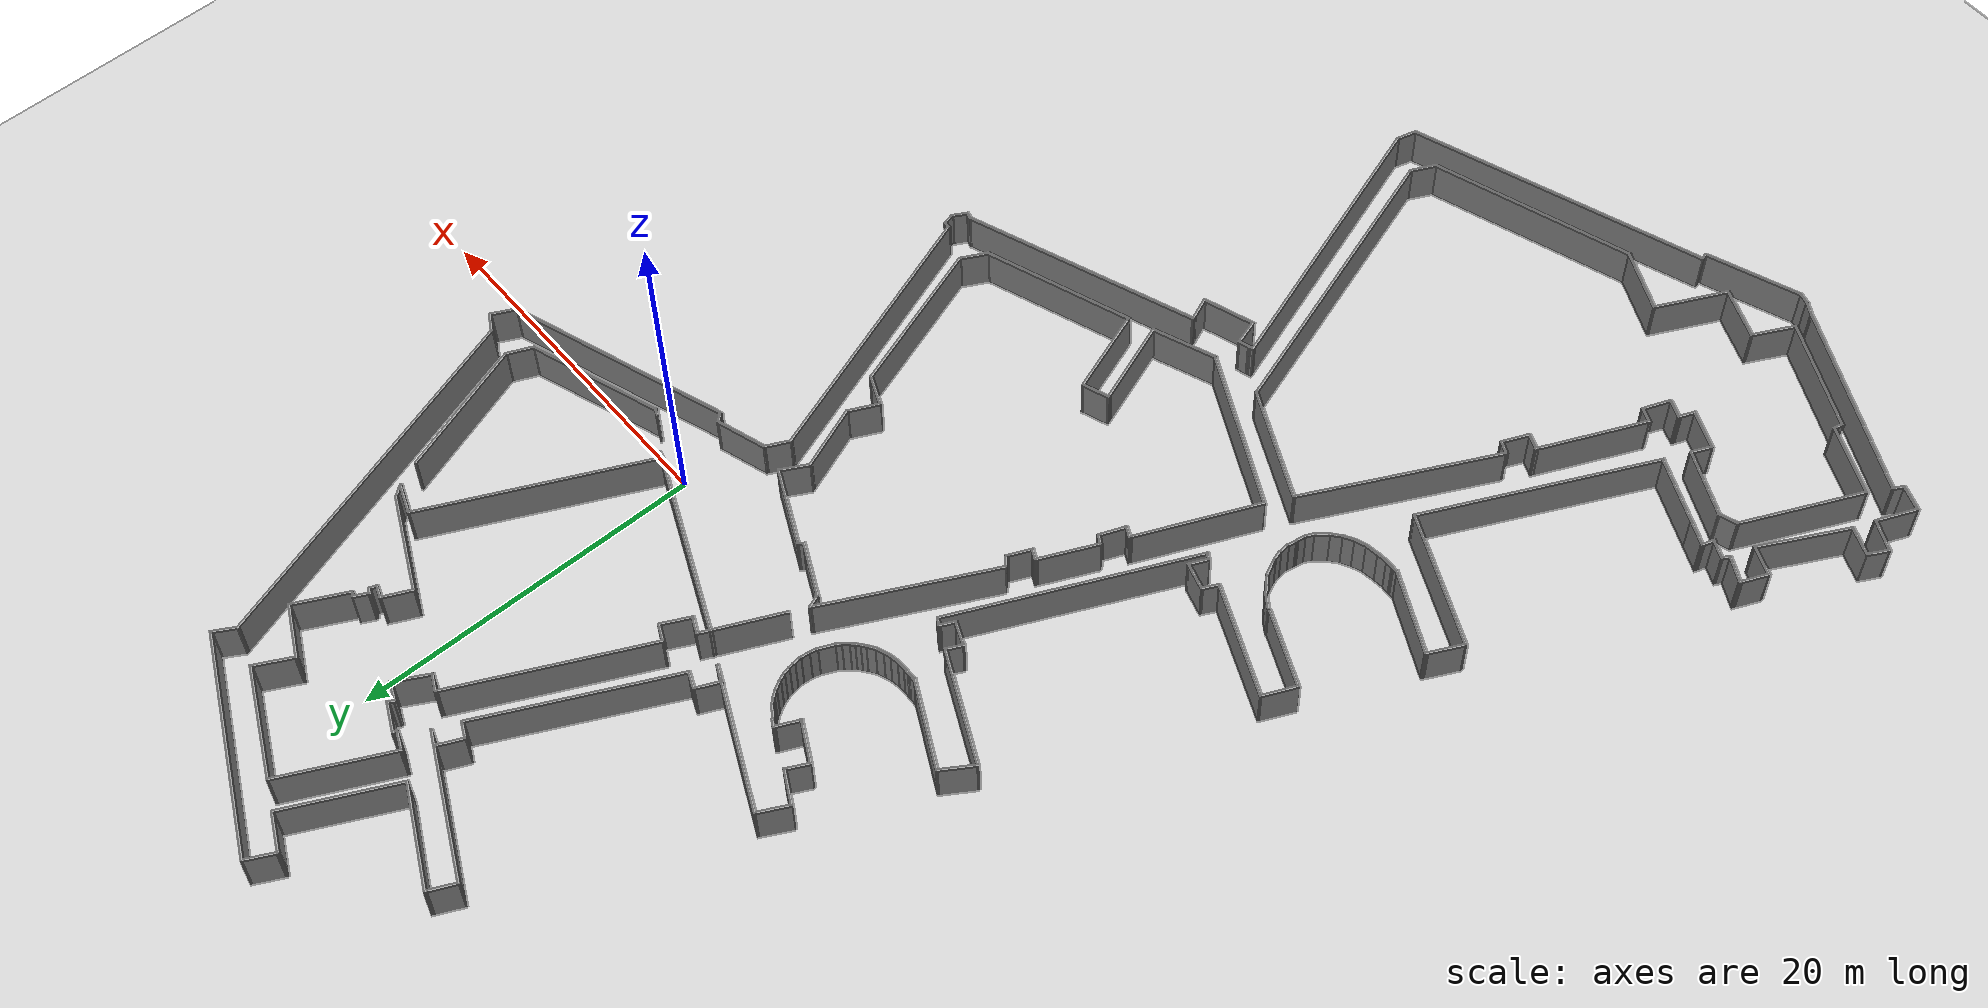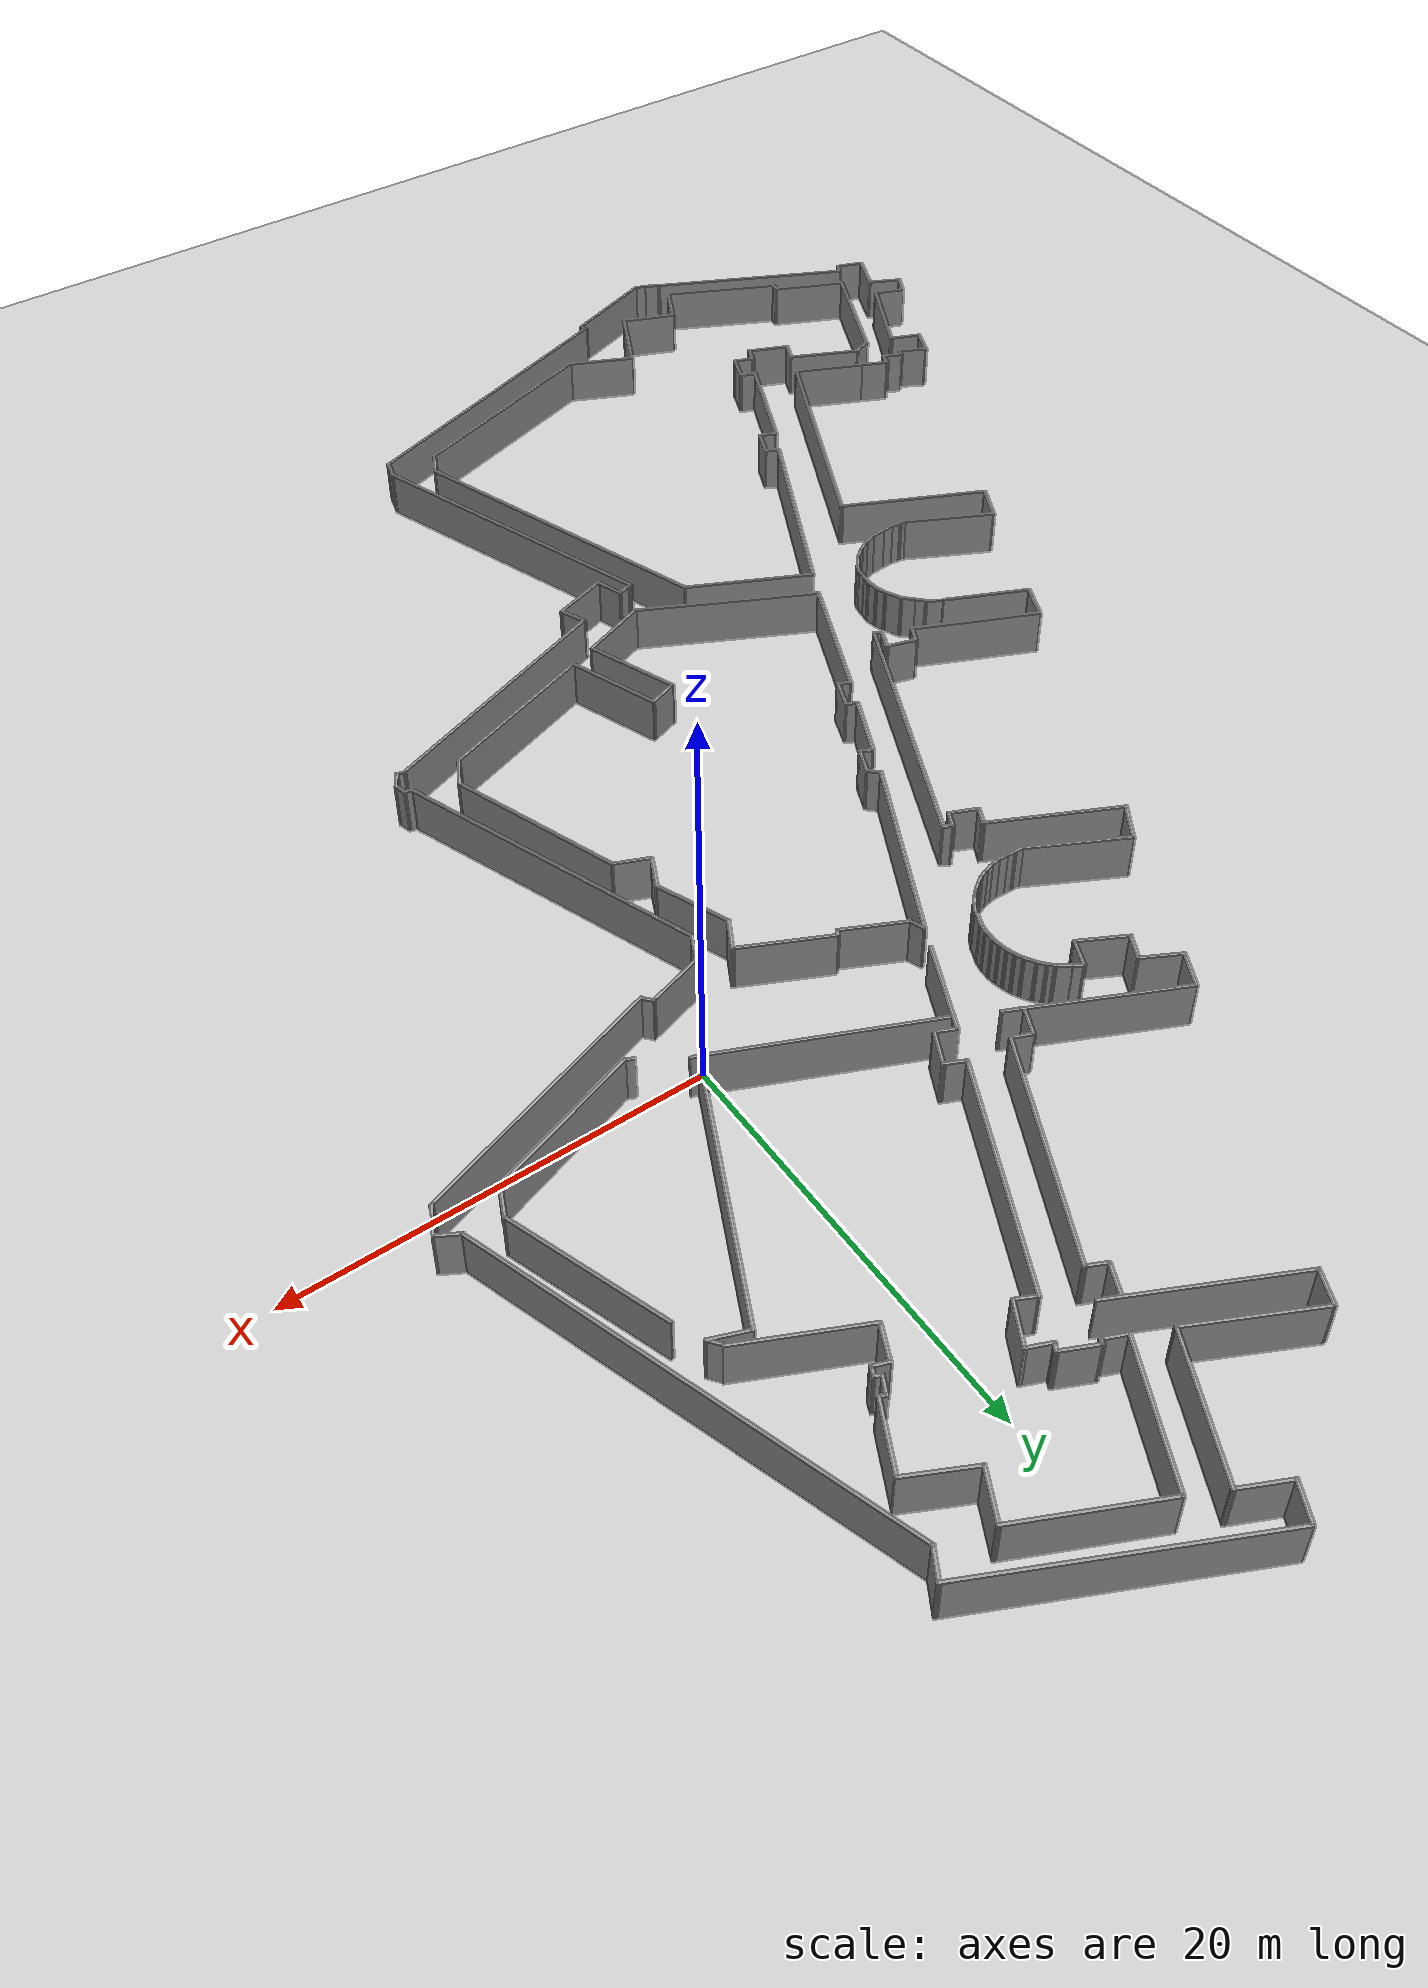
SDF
<sdf version="1.6">
 <world name="default">
  <light name="sun" type="directional">
   <pose>0 0 10 0 -0 0</pose>
   <diffuse>0.8 0.8 0.8 1</diffuse>
   <specular>0.1 0.1 0.1 1</specular>
   <attenuation>
    <range>1000</range>
    <constant>0.9</constant>
    <linear>0.01</linear>
    <quadratic>0.001</quadratic>
   </attenuation>
   <direction>-0.5 0.5 -1</direction>
  </light>
  <model name="ground_plane">
   <static>1</static>
   <link name="link">
    <collision name="collision">
     <geometry><plane><normal>0 0 1</normal><size>100 100</size></plane></geometry>
     <surface><friction><ode><mu>100</mu><mu2>50</mu2></ode></friction></surface>
    </collision>
    <visual name="visual">
     <cast_shadows>0</cast_shadows>
     <geometry><plane><normal>0 0 1</normal><size>100 100</size></plane></geometry>
     <material>
      <script><uri>file://media/materials/scripts/gazebo.material</uri><name>Gazebo/Grey</name></script>
     </material>
    </visual>
   </link>
  </model>
  <gravity>0 0 -9.8</gravity>
  <magnetic_field>6e-06 2.3e-05 -4.2e-05</magnetic_field>
  <atmosphere type="adiabatic"/>
  <physics name="default_physics" default="0" type="ode">
   <max_step_size>0.001</max_step_size>
   <real_time_factor>1</real_time_factor>
   <real_time_update_rate>1000</real_time_update_rate>
  </physics>
  <scene><ambient>0.4 0.4 0.4 1</ambient><background>0.7 0.7 0.7 1</background><shadows>1</shadows></scene>
  <spherical_coordinates>
   <surface_model>EARTH_WGS84</surface_model>
   <latitude_deg>0</latitude_deg>
   <longitude_deg>0</longitude_deg>
   <elevation>0</elevation>
   <heading_deg>0</heading_deg>
  </spherical_coordinates>
  <model name="3rd_floor">
   <pose>-15.2077 -10.9942 0 0 -0 0</pose>
   <link name="Wall_10">
    <collision name="Wall_10_Collision">
     <geometry><box><size>13.264 0.15 2.5</size></box></geometry>
     <pose>0 0 1.25 0 -0 0</pose>
    </collision>
    <visual name="Wall_10_Visual">
     <pose>0 0 1.25 0 -0 0</pose>
     <geometry><box><size>13.264 0.15 2.5</size></box></geometry>
     <material>
      <script><uri>file://media/materials/scripts/gazebo.material</uri><name>Gazebo/Grey</name></script>
      <ambient>1 1 1 1</ambient>
     </material>
    </visual>
    <pose>22.3323 9.76472 0 0 0 -2.81688</pose>
   </link>
   <link name="Wall_100">
    <collision name="Wall_100_Collision">
     <geometry><box><size>0.976108 0.15 2.5</size></box></geometry>
     <pose>0 0 1.25 0 -0 0</pose>
    </collision>
    <visual name="Wall_100_Visual">
     <pose>0 0 1.25 0 -0 0</pose>
     <geometry><box><size>0.976108 0.15 2.5</size></box></geometry>
     <material>
      <script><uri>file://media/materials/scripts/gazebo.material</uri><name>Gazebo/Grey</name></script>
      <ambient>1 1 1 1</ambient>
     </material>
    </visual>
    <pose>19.0343 28.1609 0 0 0 -2.05279</pose>
   </link>
   <link name="Wall_101">
    <collision name="Wall_101_Collision">
     <geometry><box><size>0.451187 0.15 2.5</size></box></geometry>
     <pose>0 0 1.25 0 -0 0</pose>
    </collision>
    <visual name="Wall_101_Visual">
     <pose>0 0 1.25 0 -0 0</pose>
     <geometry><box><size>0.451187 0.15 2.5</size></box></geometry>
     <material>
      <script><uri>file://media/materials/scripts/gazebo.material</uri><name>Gazebo/Grey</name></script>
      <ambient>1 1 1 1</ambient>
     </material>
    </visual>
    <pose>18.9794 27.7315 0 0 0 -0.434533</pose>
   </link>
   <link name="Wall_102">
    <collision name="Wall_102_Collision">
     <geometry><box><size>0.575251 0.15 2.5</size></box></geometry>
     <pose>0 0 1.25 0 -0 0</pose>
    </collision>
    <visual name="Wall_102_Visual">
     <pose>0 0 1.25 0 -0 0</pose>
     <geometry><box><size>0.575251 0.15 2.5</size></box></geometry>
     <material>
      <script><uri>file://media/materials/scripts/gazebo.material</uri><name>Gazebo/Grey</name></script>
      <ambient>1 1 1 1</ambient>
     </material>
    </visual>
    <pose>19.035 27.4715 0 0 0 -1.9614</pose>
   </link>
   <link name="Wall_103">
    <collision name="Wall_103_Collision">
     <geometry><box><size>0.867422 0.15 2.5</size></box></geometry>
     <pose>0 0 1.25 0 -0 0</pose>
    </collision>
    <visual name="Wall_103_Visual">
     <pose>0 0 1.25 0 -0 0</pose>
     <geometry><box><size>0.867422 0.15 2.5</size></box></geometry>
     <material>
      <script><uri>file://media/materials/scripts/gazebo.material</uri><name>Gazebo/Grey</name></script>
      <ambient>1 1 1 1</ambient>
     </material>
    </visual>
    <pose>18.6187 27.4021 0 0 -0 2.77905</pose>
   </link>
   <link name="Wall_104">
    <collision name="Wall_104_Collision">
     <geometry><box><size>1.83663 0.15 2.5</size></box></geometry>
     <pose>0 0 1.25 0 -0 0</pose>
    </collision>
    <visual name="Wall_104_Visual">
     <pose>0 0 1.25 0 -0 0</pose>
     <geometry><box><size>1.83663 0.15 2.5</size></box></geometry>
     <material>
      <script><uri>file://media/materials/scripts/gazebo.material</uri><name>Gazebo/Grey</name></script>
      <ambient>1 1 1 1</ambient>
     </material>
    </visual>
    <pose>17.9248 26.766 0 0 0 -2.00991</pose>
   </link>
   <link name="Wall_105">
    <collision name="Wall_105_Collision">
     <geometry><box><size>5.97757 0.15 2.5</size></box></geometry>
     <pose>0 0 1.25 0 -0 0</pose>
    </collision>
    <visual name="Wall_105_Visual">
     <pose>0 0 1.25 0 -0 0</pose>
     <geometry><box><size>5.97757 0.15 2.5</size></box></geometry>
     <material>
      <script><uri>file://media/materials/scripts/gazebo.material</uri><name>Gazebo/Grey</name></script>
      <ambient>1 1 1 1</ambient>
     </material>
    </visual>
    <pose>20.1971 24.7502 0 0 0 -0.444326</pose>
   </link>
   <link name="Wall_11">
    <collision name="Wall_11_Collision">
     <geometry><box><size>0.704563 0.15 2.5</size></box></geometry>
     <pose>0 0 1.25 0 -0 0</pose>
    </collision>
    <visual name="Wall_11_Visual">
     <pose>0 0 1.25 0 -0 0</pose>
     <geometry><box><size>0.704563 0.15 2.5</size></box></geometry>
     <material>
      <script><uri>file://media/materials/scripts/gazebo.material</uri><name>Gazebo/Grey</name></script>
      <ambient>1 1 1 1</ambient>
     </material>
    </visual>
    <pose>15.9334 7.89717 0 0 -0 2.29921</pose>
   </link>
   <link name="Wall_12">
    <collision name="Wall_12_Collision">
     <geometry><box><size>3.04965 0.15 2.5</size></box></geometry>
     <pose>0 0 1.25 0 -0 0</pose>
    </collision>
    <visual name="Wall_12_Visual">
     <pose>0 0 1.25 0 -0 0</pose>
     <geometry><box><size>3.04965 0.15 2.5</size></box></geometry>
     <material>
      <script><uri>file://media/materials/scripts/gazebo.material</uri><name>Gazebo/Grey</name></script>
      <ambient>1 1 1 1</ambient>
     </material>
    </visual>
    <pose>14.3645 7.6734 0 0 0 -2.83997</pose>
   </link>
   <link name="Wall_13">
    <collision name="Wall_13_Collision">
     <geometry><box><size>1.54276 0.15 2.5</size></box></geometry>
     <pose>0 0 1.25 0 -0 0</pose>
    </collision>
    <visual name="Wall_13_Visual">
     <pose>0 0 1.25 0 -0 0</pose>
     <geometry><box><size>1.54276 0.15 2.5</size></box></geometry>
     <material>
      <script><uri>file://media/materials/scripts/gazebo.material</uri><name>Gazebo/Grey</name></script>
      <ambient>1 1 1 1</ambient>
     </material>
    </visual>
    <pose>12.6693 6.61951 0 0 0 -2.0334</pose>
   </link>
   <link name="Wall_14">
    <collision name="Wall_14_Collision">
     <geometry><box><size>16.212 0.15 2.5</size></box></geometry>
     <pose>0 0 1.25 0 -0 0</pose>
    </collision>
    <visual name="Wall_14_Visual">
     <pose>0 0 1.25 0 -0 0</pose>
     <geometry><box><size>16.212 0.15 2.5</size></box></geometry>
     <material>
      <script><uri>file://media/materials/scripts/gazebo.material</uri><name>Gazebo/Grey</name></script>
      <ambient>1 1 1 1</ambient>
     </material>
    </visual>
    <pose>15.0905 -1.55572 0 0 0 -1.22369</pose>
   </link>
   <link name="Wall_15">
    <collision name="Wall_15_Collision">
     <geometry><box><size>0.5 0.15 2.5</size></box></geometry>
     <pose>0 0 1.25 0 -0 0</pose>
    </collision>
    <visual name="Wall_15_Visual">
     <pose>0 0 1.25 0 -0 0</pose>
     <geometry><box><size>0.5 0.15 2.5</size></box></geometry>
     <material>
      <script><uri>file://media/materials/scripts/gazebo.material</uri><name>Gazebo/Grey</name></script>
      <ambient>1 1 1 1</ambient>
     </material>
    </visual>
    <pose>17.9914 -9.15306 0 0 0 -0.261799</pose>
   </link>
   <link name="Wall_16">
    <collision name="Wall_16_Collision">
     <geometry><box><size>0.75 0.15 2.5</size></box></geometry>
     <pose>0 0 1.25 0 -0 0</pose>
    </collision>
    <visual name="Wall_16_Visual">
     <pose>0 0 1.25 0 -0 0</pose>
     <geometry><box><size>0.75 0.15 2.5</size></box></geometry>
     <material>
      <script><uri>file://media/materials/scripts/gazebo.material</uri><name>Gazebo/Grey</name></script>
      <ambient>1 1 1 1</ambient>
     </material>
    </visual>
    <pose>18.2381 -9.48813 0 0 0 -1.309</pose>
   </link>
   <link name="Wall_17">
    <collision name="Wall_17_Collision">
     <geometry><box><size>1 0.15 2.5</size></box></geometry>
     <pose>0 0 1.25 0 -0 0</pose>
    </collision>
    <visual name="Wall_17_Visual">
     <pose>0 0 1.25 0 -0 0</pose>
     <geometry><box><size>1 0.15 2.5</size></box></geometry>
     <material>
      <script><uri>file://media/materials/scripts/gazebo.material</uri><name>Gazebo/Grey</name></script>
      <ambient>1 1 1 1</ambient>
     </material>
    </visual>
    <pose>18.1033 -10.146 0 0 0 -2.0944</pose>
   </link>
   <link name="Wall_18">
    <collision name="Wall_18_Collision">
     <geometry><box><size>0.5 0.15 2.5</size></box></geometry>
     <pose>0 0 1.25 0 -0 0</pose>
    </collision>
    <visual name="Wall_18_Visual">
     <pose>0 0 1.25 0 -0 0</pose>
     <geometry><box><size>0.5 0.15 2.5</size></box></geometry>
     <material>
      <script><uri>file://media/materials/scripts/gazebo.material</uri><name>Gazebo/Grey</name></script>
      <ambient>1 1 1 1</ambient>
     </material>
    </visual>
    <pose>17.7217 -10.4687 0 0 -0 2.87979</pose>
   </link>
   <link name="Wall_19">
    <collision name="Wall_19_Collision">
     <geometry><box><size>13.8931 0.15 2.5</size></box></geometry>
     <pose>0 0 1.25 0 -0 0</pose>
    </collision>
    <visual name="Wall_19_Visual">
     <pose>0 0 1.25 0 -0 0</pose>
     <geometry><box><size>13.8931 0.15 2.5</size></box></geometry>
     <material>
      <script><uri>file://media/materials/scripts/gazebo.material</uri><name>Gazebo/Grey</name></script>
      <ambient>1 1 1 1</ambient>
     </material>
    </visual>
    <pose>11.0965 -12.7763 0 0 0 -2.79211</pose>
   </link>
   <link name="Wall_20">
    <collision name="Wall_20_Collision">
     <geometry><box><size>1.53196 0.15 2.5</size></box></geometry>
     <pose>0 0 1.25 0 -0 0</pose>
    </collision>
    <visual name="Wall_20_Visual">
     <pose>0 0 1.25 0 -0 0</pose>
     <geometry><box><size>1.53196 0.15 2.5</size></box></geometry>
     <material>
      <script><uri>file://media/materials/scripts/gazebo.material</uri><name>Gazebo/Grey</name></script>
      <ambient>1 1 1 1</ambient>
     </material>
    </visual>
    <pose>4.90091 -15.7692 0 0 0 -1.18415</pose>
   </link>
   <link name="Wall_21">
    <collision name="Wall_21_Collision">
     <geometry><box><size>3.11935 0.15 2.5</size></box></geometry>
     <pose>0 0 1.25 0 -0 0</pose>
    </collision>
    <visual name="Wall_21_Visual">
     <pose>0 0 1.25 0 -0 0</pose>
     <geometry><box><size>3.11935 0.15 2.5</size></box></geometry>
     <material>
      <script><uri>file://media/materials/scripts/gazebo.material</uri><name>Gazebo/Grey</name></script>
      <ambient>1 1 1 1</ambient>
     </material>
    </visual>
    <pose>3.75166 -16.8746 0 0 0 -2.82267</pose>
   </link>
   <link name="Wall_22">
    <collision name="Wall_22_Collision">
     <geometry><box><size>1.5718 0.15 2.5</size></box></geometry>
     <pose>0 0 1.25 0 -0 0</pose>
    </collision>
    <visual name="Wall_22_Visual">
     <pose>0 0 1.25 0 -0 0</pose>
     <geometry><box><size>1.5718 0.15 2.5</size></box></geometry>
     <material>
      <script><uri>file://media/materials/scripts/gazebo.material</uri><name>Gazebo/Grey</name></script>
      <ambient>1 1 1 1</ambient>
     </material>
    </visual>
    <pose>2.12904 -16.6618 0 0 -0 1.8748</pose>
   </link>
   <link name="Wall_23">
    <collision name="Wall_23_Collision">
     <geometry><box><size>0.75 0.15 2.5</size></box></geometry>
     <pose>0 0 1.25 0 -0 0</pose>
    </collision>
    <visual name="Wall_23_Visual">
     <pose>0 0 1.25 0 -0 0</pose>
     <geometry><box><size>0.75 0.15 2.5</size></box></geometry>
     <material>
      <script><uri>file://media/materials/scripts/gazebo.material</uri><name>Gazebo/Grey</name></script>
      <ambient>1 1 1 1</ambient>
     </material>
    </visual>
    <pose>1.62646 -16.0612 0 0 0 -2.87979</pose>
   </link>
   <link name="Wall_24">
    <collision name="Wall_24_Collision">
     <geometry><box><size>0.384084 0.15 2.5</size></box></geometry>
     <pose>0 0 1.25 0 -0 0</pose>
    </collision>
    <visual name="Wall_24_Visual">
     <pose>0 0 1.25 0 -0 0</pose>
     <geometry><box><size>0.384084 0.15 2.5</size></box></geometry>
     <material>
      <script><uri>file://media/materials/scripts/gazebo.material</uri><name>Gazebo/Grey</name></script>
      <ambient>1 1 1 1</ambient>
     </material>
    </visual>
    <pose>1.22746 -16.1809 0 0 0 -2.77406</pose>
   </link>
   <link name="Wall_28">
    <collision name="Wall_28_Collision">
     <geometry><box><size>16.723 0.15 2.5</size></box></geometry>
     <pose>0 0 1.25 0 -0 0</pose>
    </collision>
    <visual name="Wall_28_Visual">
     <pose>0 0 1.25 0 -0 0</pose>
     <geometry><box><size>16.723 0.15 2.5</size></box></geometry>
     <material>
      <script><uri>file://media/materials/scripts/gazebo.material</uri><name>Gazebo/Grey</name></script>
      <ambient>1 1 1 1</ambient>
     </material>
    </visual>
    <pose>3.78987 -24.0669 0 0 0 -1.24252</pose>
   </link>
   <link name="Wall_29">
    <collision name="Wall_29_Collision">
     <geometry><box><size>1.25 0.15 2.5</size></box></geometry>
     <pose>0 0 1.25 0 -0 0</pose>
    </collision>
    <visual name="Wall_29_Visual">
     <pose>0 0 1.25 0 -0 0</pose>
     <geometry><box><size>1.25 0.15 2.5</size></box></geometry>
     <material>
      <script><uri>file://media/materials/scripts/gazebo.material</uri><name>Gazebo/Grey</name></script>
      <ambient>1 1 1 1</ambient>
     </material>
    </visual>
    <pose>6.31916 -32.4422 0 0 0 -1.8326</pose>
   </link>
   <link name="Wall_30">
    <collision name="Wall_30_Collision">
     <geometry><box><size>17.4996 0.15 2.5</size></box></geometry>
     <pose>0 0 1.25 0 -0 0</pose>
    </collision>
    <visual name="Wall_30_Visual">
     <pose>0 0 1.25 0 -0 0</pose>
     <geometry><box><size>17.4996 0.15 2.5</size></box></geometry>
     <material>
      <script><uri>file://media/materials/scripts/gazebo.material</uri><name>Gazebo/Grey</name></script>
      <ambient>1 1 1 1</ambient>
     </material>
    </visual>
    <pose>-2.02263 -35.8056 0 0 0 -2.80901</pose>
   </link>
   <link name="Wall_31">
    <collision name="Wall_31_Collision">
     <geometry><box><size>0.5 0.15 2.5</size></box></geometry>
     <pose>0 0 1.25 0 -0 0</pose>
    </collision>
    <visual name="Wall_31_Visual">
     <pose>0 0 1.25 0 -0 0</pose>
     <geometry><box><size>0.5 0.15 2.5</size></box></geometry>
     <material>
      <script><uri>file://media/materials/scripts/gazebo.material</uri><name>Gazebo/Grey</name></script>
      <ambient>1 1 1 1</ambient>
     </material>
    </visual>
    <pose>-10.1768 -38.8068 0 0 0 -1.309</pose>
   </link>
   <link name="Wall_32">
    <collision name="Wall_32_Collision">
     <geometry><box><size>5.63609 0.15 2.5</size></box></geometry>
     <pose>0 0 1.25 0 -0 0</pose>
    </collision>
    <visual name="Wall_32_Visual">
     <pose>0 0 1.25 0 -0 0</pose>
     <geometry><box><size>5.63609 0.15 2.5</size></box></geometry>
     <material>
      <script><uri>file://media/materials/scripts/gazebo.material</uri><name>Gazebo/Grey</name></script>
      <ambient>1 1 1 1</ambient>
     </material>
    </visual>
    <pose>-12.7033 -39.9297 0 0 0 -2.78643</pose>
   </link>
   <link name="Wall_33">
    <collision name="Wall_33_Collision">
     <geometry><box><size>0.75 0.15 2.5</size></box></geometry>
     <pose>0 0 1.25 0 -0 0</pose>
    </collision>
    <visual name="Wall_33_Visual">
     <pose>0 0 1.25 0 -0 0</pose>
     <geometry><box><size>0.75 0.15 2.5</size></box></geometry>
     <material>
      <script><uri>file://media/materials/scripts/gazebo.material</uri><name>Gazebo/Grey</name></script>
      <ambient>1 1 1 1</ambient>
     </material>
    </visual>
    <pose>-15.565 -40.806 0 0 -0 2.87979</pose>
   </link>
   <link name="Wall_34">
    <collision name="Wall_34_Collision">
     <geometry><box><size>1 0.15 2.5</size></box></geometry>
     <pose>0 0 1.25 0 -0 0</pose>
    </collision>
    <visual name="Wall_34_Visual">
     <pose>0 0 1.25 0 -0 0</pose>
     <geometry><box><size>1 0.15 2.5</size></box></geometry>
     <material>
      <script><uri>file://media/materials/scripts/gazebo.material</uri><name>Gazebo/Grey</name></script>
      <ambient>1 1 1 1</ambient>
     </material>
    </visual>
    <pose>-16.2228 -40.5158 0 0 -0 2.61799</pose>
   </link>
   <link name="Wall_35">
    <collision name="Wall_35_Collision">
     <geometry><box><size>11.5195 0.15 2.5</size></box></geometry>
     <pose>0 0 1.25 0 -0 0</pose>
    </collision>
    <visual name="Wall_35_Visual">
     <pose>0 0 1.25 0 -0 0</pose>
     <geometry><box><size>11.5195 0.15 2.5</size></box></geometry>
     <material>
      <script><uri>file://media/materials/scripts/gazebo.material</uri><name>Gazebo/Grey</name></script>
      <ambient>1 1 1 1</ambient>
     </material>
    </visual>
    <pose>-21.688 -37.7862 0 0 -0 2.68289</pose>
   </link>
   <link name="Wall_36">
    <collision name="Wall_36_Collision">
     <geometry><box><size>0.75 0.15 2.5</size></box></geometry>
     <pose>0 0 1.25 0 -0 0</pose>
    </collision>
    <visual name="Wall_36_Visual">
     <pose>0 0 1.25 0 -0 0</pose>
     <geometry><box><size>0.75 0.15 2.5</size></box></geometry>
     <material>
      <script><uri>file://media/materials/scripts/gazebo.material</uri><name>Gazebo/Grey</name></script>
      <ambient>1 1 1 1</ambient>
     </material>
    </visual>
    <pose>-26.935 -35.5288 0 0 0 -2.0944</pose>
   </link>
   <link name="Wall_37">
    <collision name="Wall_37_Collision">
     <geometry><box><size>1.62868 0.15 2.5</size></box></geometry>
     <pose>0 0 1.25 0 -0 0</pose>
    </collision>
    <visual name="Wall_37_Visual">
     <pose>0 0 1.25 0 -0 0</pose>
     <geometry><box><size>1.62868 0.15 2.5</size></box></geometry>
     <material>
      <script><uri>file://media/materials/scripts/gazebo.material</uri><name>Gazebo/Grey</name></script>
      <ambient>1 1 1 1</ambient>
     </material>
    </visual>
    <pose>-27.7772 -35.5288 0 0 -0 2.78252</pose>
   </link>
   <link name="Wall_38">
    <collision name="Wall_38_Collision">
     <geometry><box><size>2.49688 0.15 2.5</size></box></geometry>
     <pose>0 0 1.25 0 -0 0</pose>
    </collision>
    <visual name="Wall_38_Visual">
     <pose>0 0 1.25 0 -0 0</pose>
     <geometry><box><size>2.49688 0.15 2.5</size></box></geometry>
     <material>
      <script><uri>file://media/materials/scripts/gazebo.material</uri><name>Gazebo/Grey</name></script>
      <ambient>1 1 1 1</ambient>
     </material>
    </visual>
    <pose>-28.0015 -34.1929 0 0 -0 1.16067</pose>
   </link>
   <link name="Wall_39">
    <collision name="Wall_39_Collision">
     <geometry><box><size>1.99764 0.15 2.5</size></box></geometry>
     <pose>0 0 1.25 0 -0 0</pose>
    </collision>
    <visual name="Wall_39_Visual">
     <pose>0 0 1.25 0 -0 0</pose>
     <geometry><box><size>1.99764 0.15 2.5</size></box></geometry>
     <material>
      <script><uri>file://media/materials/scripts/gazebo.material</uri><name>Gazebo/Grey</name></script>
      <ambient>1 1 1 1</ambient>
     </material>
    </visual>
    <pose>-28.363 -32.7098 0 0 -0 2.68543</pose>
   </link>
   <link name="Wall_40">
    <collision name="Wall_40_Collision">
     <geometry><box><size>1.34318 0.15 2.5</size></box></geometry>
     <pose>0 0 1.25 0 -0 0</pose>
    </collision>
    <visual name="Wall_40_Visual">
     <pose>0 0 1.25 0 -0 0</pose>
     <geometry><box><size>1.34318 0.15 2.5</size></box></geometry>
     <material>
      <script><uri>file://media/materials/scripts/gazebo.material</uri><name>Gazebo/Grey</name></script>
      <ambient>1 1 1 1</ambient>
     </material>
    </visual>
    <pose>-28.9077 -31.7786 0 0 -0 1.07343</pose>
   </link>
   <link name="Wall_41">
    <collision name="Wall_41_Collision">
     <geometry><box><size>1.82539 0.15 2.5</size></box></geometry>
     <pose>0 0 1.25 0 -0 0</pose>
    </collision>
    <visual name="Wall_41_Visual">
     <pose>0 0 1.25 0 -0 0</pose>
     <geometry><box><size>1.82539 0.15 2.5</size></box></geometry>
     <material>
      <script><uri>file://media/materials/scripts/gazebo.material</uri><name>Gazebo/Grey</name></script>
      <ambient>1 1 1 1</ambient>
     </material>
    </visual>
    <pose>-27.8387 -31.5773 0 0 0 -0.395858</pose>
   </link>
   <link name="Wall_42">
    <collision name="Wall_42_Collision">
     <geometry><box><size>5.40682 0.15 2.5</size></box></geometry>
     <pose>0 0 1.25 0 -0 0</pose>
    </collision>
    <visual name="Wall_42_Visual">
     <pose>0 0 1.25 0 -0 0</pose>
     <geometry><box><size>5.40682 0.15 2.5</size></box></geometry>
     <material>
      <script><uri>file://media/materials/scripts/gazebo.material</uri><name>Gazebo/Grey</name></script>
      <ambient>1 1 1 1</ambient>
     </material>
    </visual>
    <pose>-25.8364 -29.5771 0 0 -0 1.08409</pose>
   </link>
   <link name="Wall_43">
    <collision name="Wall_43_Collision">
     <geometry><box><size>1.86837 0.15 2.5</size></box></geometry>
     <pose>0 0 1.25 0 -0 0</pose>
    </collision>
    <visual name="Wall_43_Visual">
     <pose>0 0 1.25 0 -0 0</pose>
     <geometry><box><size>1.86837 0.15 2.5</size></box></geometry>
     <material>
      <script><uri>file://media/materials/scripts/gazebo.material</uri><name>Gazebo/Grey</name></script>
      <ambient>1 1 1 1</ambient>
     </material>
    </visual>
    <pose>-25.3986 -26.9197 0 0 -0 2.74208</pose>
   </link>
   <link name="Wall_44">
    <collision name="Wall_44_Collision">
     <geometry><box><size>1.72521 0.15 2.5</size></box></geometry>
     <pose>0 0 1.25 0 -0 0</pose>
    </collision>
    <visual name="Wall_44_Visual">
     <pose>0 0 1.25 0 -0 0</pose>
     <geometry><box><size>1.72521 0.15 2.5</size></box></geometry>
     <material>
      <script><uri>file://media/materials/scripts/gazebo.material</uri><name>Gazebo/Grey</name></script>
      <ambient>1 1 1 1</ambient>
     </material>
    </visual>
    <pose>-25.8735 -25.8643 0 0 -0 1.15711</pose>
   </link>
   <link name="Wall_45">
    <collision name="Wall_45_Collision">
     <geometry><box><size>1.70823 0.15 2.5</size></box></geometry>
     <pose>0 0 1.25 0 -0 0</pose>
    </collision>
    <visual name="Wall_45_Visual">
     <pose>0 0 1.25 0 -0 0</pose>
     <geometry><box><size>1.70823 0.15 2.5</size></box></geometry>
     <material>
      <script><uri>file://media/materials/scripts/gazebo.material</uri><name>Gazebo/Grey</name></script>
      <ambient>1 1 1 1</ambient>
     </material>
    </visual>
    <pose>-24.8709 -25.5125 0 0 0 -0.493941</pose>
   </link>
   <link name="Wall_46">
    <collision name="Wall_46_Collision">
     <geometry><box><size>0.590789 0.15 2.5</size></box></geometry>
     <pose>0 0 1.25 0 -0 0</pose>
    </collision>
    <visual name="Wall_46_Visual">
     <pose>0 0 1.25 0 -0 0</pose>
     <geometry><box><size>0.590789 0.15 2.5</size></box></geometry>
     <material>
      <script><uri>file://media/materials/scripts/gazebo.material</uri><name>Gazebo/Grey</name></script>
      <ambient>1 1 1 1</ambient>
     </material>
    </visual>
    <pose>-24.0794 -25.6884 0 0 -0 1.07145</pose>
   </link>
   <link name="Wall_47">
    <collision name="Wall_47_Collision">
     <geometry><box><size>1.23599 0.15 2.5</size></box></geometry>
     <pose>0 0 1.25 0 -0 0</pose>
    </collision>
    <visual name="Wall_47_Visual">
     <pose>0 0 1.25 0 -0 0</pose>
     <geometry><box><size>1.23599 0.15 2.5</size></box></geometry>
     <material>
      <script><uri>file://media/materials/scripts/gazebo.material</uri><name>Gazebo/Grey</name></script>
      <ambient>1 1 1 1</ambient>
     </material>
    </visual>
    <pose>-23.4814 -25.7236 0 0 0 -0.43467</pose>
   </link>
   <link name="Wall_471">
    <collision name="Wall_471_Collision">
     <geometry><box><size>6.6762 0.15 2.5</size></box></geometry>
     <pose>0 0 1.25 0 -0 0</pose>
    </collision>
    <visual name="Wall_471_Visual">
     <pose>0 0 1.25 0 -0 0</pose>
     <geometry><box><size>6.6762 0.15 2.5</size></box></geometry>
     <material>
      <script><uri>file://media/materials/scripts/gazebo.material</uri><name>Gazebo/Grey</name></script>
      <ambient>1 1 1 1</ambient>
     </material>
    </visual>
    <pose>11.7969 34.5955 0 0 0 -2.02918</pose>
   </link>
   <link name="Wall_472">
    <collision name="Wall_472_Collision">
     <geometry><box><size>1.25496 0.15 2.5</size></box></geometry>
     <pose>0 0 1.25 0 -0 0</pose>
    </collision>
    <visual name="Wall_472_Visual">
     <pose>0 0 1.25 0 -0 0</pose>
     <geometry><box><size>1.25496 0.15 2.5</size></box></geometry>
     <material>
      <script><uri>file://media/materials/scripts/gazebo.material</uri><name>Gazebo/Grey</name></script>
      <ambient>1 1 1 1</ambient>
     </material>
    </visual>
    <pose>10.8587 31.4468 0 0 0 -0.414507</pose>
   </link>
   <link name="Wall_473">
    <collision name="Wall_473_Collision">
     <geometry><box><size>0.36786 0.15 2.5</size></box></geometry>
     <pose>0 0 1.25 0 -0 0</pose>
    </collision>
    <visual name="Wall_473_Visual">
     <pose>0 0 1.25 0 -0 0</pose>
     <geometry><box><size>0.36786 0.15 2.5</size></box></geometry>
     <material>
      <script><uri>file://media/materials/scripts/gazebo.material</uri><name>Gazebo/Grey</name></script>
      <ambient>1 1 1 1</ambient>
     </material>
    </visual>
    <pose>11.4048 31.3254 0 0 -0 1.19029</pose>
   </link>
   <link name="Wall_474">
    <collision name="Wall_474_Collision">
     <geometry><box><size>1.91369 0.15 2.5</size></box></geometry>
     <pose>0 0 1.25 0 -0 0</pose>
    </collision>
    <visual name="Wall_474_Visual">
     <pose>0 0 1.25 0 -0 0</pose>
     <geometry><box><size>1.91369 0.15 2.5</size></box></geometry>
     <material>
      <script><uri>file://media/materials/scripts/gazebo.material</uri><name>Gazebo/Grey</name></script>
      <ambient>1 1 1 1</ambient>
     </material>
    </visual>
    <pose>12.2424 31.0494 0 0 0 -0.441999</pose>
   </link>
   <link name="Wall_475">
    <collision name="Wall_475_Collision">
     <geometry><box><size>0.514278 0.15 2.5</size></box></geometry>
     <pose>0 0 1.25 0 -0 0</pose>
    </collision>
    <visual name="Wall_475_Visual">
     <pose>0 0 1.25 0 -0 0</pose>
     <geometry><box><size>0.514278 0.15 2.5</size></box></geometry>
     <material>
      <script><uri>file://media/materials/scripts/gazebo.material</uri><name>Gazebo/Grey</name></script>
      <ambient>1 1 1 1</ambient>
     </material>
    </visual>
    <pose>12.9501 30.5134 0 0 0 -2.08355</pose>
   </link>
   <link name="Wall_476">
    <collision name="Wall_476_Collision">
     <geometry><box><size>1.29211 0.15 2.5</size></box></geometry>
     <pose>0 0 1.25 0 -0 0</pose>
    </collision>
    <visual name="Wall_476_Visual">
     <pose>0 0 1.25 0 -0 0</pose>
     <geometry><box><size>1.29211 0.15 2.5</size></box></geometry>
     <material>
      <script><uri>file://media/materials/scripts/gazebo.material</uri><name>Gazebo/Grey</name></script>
      <ambient>1 1 1 1</ambient>
     </material>
    </visual>
    <pose>13.3767 30.1322 0 0 0 -0.400241</pose>
   </link>
   <link name="Wall_477">
    <collision name="Wall_477_Collision">
     <geometry><box><size>2.25026 0.15 2.5</size></box></geometry>
     <pose>0 0 1.25 0 -0 0</pose>
    </collision>
    <visual name="Wall_477_Visual">
     <pose>0 0 1.25 0 -0 0</pose>
     <geometry><box><size>2.25026 0.15 2.5</size></box></geometry>
     <material>
      <script><uri>file://media/materials/scripts/gazebo.material</uri><name>Gazebo/Grey</name></script>
      <ambient>1 1 1 1</ambient>
     </material>
    </visual>
    <pose>13.4071 28.9892 0 0 0 -2.07298</pose>
   </link>
   <link name="Wall_478">
    <collision name="Wall_478_Collision">
     <geometry><box><size>1.14508 0.15 2.5</size></box></geometry>
     <pose>0 0 1.25 0 -0 0</pose>
    </collision>
    <visual name="Wall_478_Visual">
     <pose>0 0 1.25 0 -0 0</pose>
     <geometry><box><size>1.14508 0.15 2.5</size></box></geometry>
     <material>
      <script><uri>file://media/materials/scripts/gazebo.material</uri><name>Gazebo/Grey</name></script>
      <ambient>1 1 1 1</ambient>
     </material>
    </visual>
    <pose>12.4566 28.2913 0 0 -0 2.67794</pose>
   </link>
   <link name="Wall_48">
    <collision name="Wall_48_Collision">
     <geometry><box><size>0.81747 0.15 2.5</size></box></geometry>
     <pose>0 0 1.25 0 -0 0</pose>
    </collision>
    <visual name="Wall_48_Visual">
     <pose>0 0 1.25 0 -0 0</pose>
     <geometry><box><size>0.81747 0.15 2.5</size></box></geometry>
     <material>
      <script><uri>file://media/materials/scripts/gazebo.material</uri><name>Gazebo/Grey</name></script>
      <ambient>1 1 1 1</ambient>
     </material>
    </visual>
    <pose>-22.8833 -25.6357 0 0 -0 1.24905</pose>
   </link>
   <link name="Wall_480">
    <collision name="Wall_480_Collision">
     <geometry><box><size>11.58 0.15 2.5</size></box></geometry>
     <pose>0 0 1.25 0 -0 0</pose>
    </collision>
    <visual name="Wall_480_Visual">
     <pose>0 0 1.25 0 -0 0</pose>
     <geometry><box><size>11.58 0.15 2.5</size></box></geometry>
     <material>
      <script><uri>file://media/materials/scripts/gazebo.material</uri><name>Gazebo/Grey</name></script>
      <ambient>1 1 1 1</ambient>
     </material>
    </visual>
    <pose>9.50935 23.3757 0 0 0 -2.024</pose>
   </link>
   <link name="Wall_481">
    <collision name="Wall_481_Collision">
     <geometry><box><size>1.15737 0.15 2.5</size></box></geometry>
     <pose>0 0 1.25 0 -0 0</pose>
    </collision>
    <visual name="Wall_481_Visual">
     <pose>0 0 1.25 0 -0 0</pose>
     <geometry><box><size>1.15737 0.15 2.5</size></box></geometry>
     <material>
      <script><uri>file://media/materials/scripts/gazebo.material</uri><name>Gazebo/Grey</name></script>
      <ambient>1 1 1 1</ambient>
     </material>
    </visual>
    <pose>7.46438 18.0266 0 0 0 -0.432408</pose>
   </link>
   <link name="Wall_482">
    <collision name="Wall_482_Collision">
     <geometry><box><size>1.88057 0.15 2.5</size></box></geometry>
     <pose>0 0 1.25 0 -0 0</pose>
    </collision>
    <visual name="Wall_482_Visual">
     <pose>0 0 1.25 0 -0 0</pose>
     <geometry><box><size>1.88057 0.15 2.5</size></box></geometry>
     <material>
      <script><uri>file://media/materials/scripts/gazebo.material</uri><name>Gazebo/Grey</name></script>
      <ambient>1 1 1 1</ambient>
     </material>
    </visual>
    <pose>7.53474 17.0416 0 0 0 -2.03444</pose>
   </link>
   <link name="Wall_483">
    <collision name="Wall_483_Collision">
     <geometry><box><size>1.1299 0.15 2.5</size></box></geometry>
     <pose>0 0 1.25 0 -0 0</pose>
    </collision>
    <visual name="Wall_483_Visual">
     <pose>0 0 1.25 0 -0 0</pose>
     <geometry><box><size>1.1299 0.15 2.5</size></box></geometry>
     <material>
      <script><uri>file://media/materials/scripts/gazebo.material</uri><name>Gazebo/Grey</name></script>
      <ambient>1 1 1 1</ambient>
     </material>
    </visual>
    <pose>6.70329 16.4738 0 0 -0 2.70736</pose>
   </link>
   <link name="Wall_485">
    <collision name="Wall_485_Collision">
     <geometry><box><size>4.80153 0.15 2.5</size></box></geometry>
     <pose>0 0 1.25 0 -0 0</pose>
    </collision>
    <visual name="Wall_485_Visual">
     <pose>0 0 1.25 0 -0 0</pose>
     <geometry><box><size>4.80153 0.15 2.5</size></box></geometry>
     <material>
      <script><uri>file://media/materials/scripts/gazebo.material</uri><name>Gazebo/Grey</name></script>
      <ambient>1 1 1 1</ambient>
     </material>
    </visual>
    <pose>5.26754 14.5719 0 0 0 -2.00697</pose>
   </link>
   <link name="Wall_487">
    <collision name="Wall_487_Collision">
     <geometry><box><size>10.9993 0.15 2.5</size></box></geometry>
     <pose>0 0 1.25 0 -0 0</pose>
    </collision>
    <visual name="Wall_487_Visual">
     <pose>0 0 1.25 0 -0 0</pose>
     <geometry><box><size>10.9993 0.15 2.5</size></box></geometry>
     <material>
      <script><uri>file://media/materials/scripts/gazebo.material</uri><name>Gazebo/Grey</name></script>
      <ambient>1 1 1 1</ambient>
     </material>
    </visual>
    <pose>10.9112 13.8828 0 0 0 -0.416814</pose>
   </link>
   <link name="Wall_489">
    <collision name="Wall_489_Collision">
     <geometry><box><size>13.3258 0.15 2.5</size></box></geometry>
     <pose>0 0 1.25 0 -0 0</pose>
    </collision>
    <visual name="Wall_489_Visual">
     <pose>0 0 1.25 0 -0 0</pose>
     <geometry><box><size>13.3258 0.15 2.5</size></box></geometry>
     <material>
      <script><uri>file://media/materials/scripts/gazebo.material</uri><name>Gazebo/Grey</name></script>
      <ambient>1 1 1 1</ambient>
     </material>
    </visual>
    <pose>18.7301 17.6221 0 0 -0 1.12195</pose>
   </link>
   <link name="Wall_49">
    <collision name="Wall_49_Collision">
     <geometry><box><size>1.66105 0.15 2.5</size></box></geometry>
     <pose>0 0 1.25 0 -0 0</pose>
    </collision>
    <visual name="Wall_49_Visual">
     <pose>0 0 1.25 0 -0 0</pose>
     <geometry><box><size>1.66105 0.15 2.5</size></box></geometry>
     <material>
      <script><uri>file://media/materials/scripts/gazebo.material</uri><name>Gazebo/Grey</name></script>
      <ambient>1 1 1 1</ambient>
     </material>
    </visual>
    <pose>-22.0918 -25.6357 0 0 0 -0.432408</pose>
   </link>
   <link name="Wall_490">
    <collision name="Wall_490_Collision">
     <geometry><box><size>1.92051 0.15 2.5</size></box></geometry>
     <pose>0 0 1.25 0 -0 0</pose>
    </collision>
    <visual name="Wall_490_Visual">
     <pose>0 0 1.25 0 -0 0</pose>
     <geometry><box><size>1.92051 0.15 2.5</size></box></geometry>
     <material>
      <script><uri>file://media/materials/scripts/gazebo.material</uri><name>Gazebo/Grey</name></script>
      <ambient>1 1 1 1</ambient>
     </material>
    </visual>
    <pose>22.4155 23.2408 0 0 0 -0.365747</pose>
   </link>
   <link name="Wall_491">
    <collision name="Wall_491_Collision">
     <geometry><box><size>0.77634 0.15 2.5</size></box></geometry>
     <pose>0 0 1.25 0 -0 0</pose>
    </collision>
    <visual name="Wall_491_Visual">
     <pose>0 0 1.25 0 -0 0</pose>
     <geometry><box><size>0.77634 0.15 2.5</size></box></geometry>
     <material>
      <script><uri>file://media/materials/scripts/gazebo.material</uri><name>Gazebo/Grey</name></script>
      <ambient>1 1 1 1</ambient>
     </material>
    </visual>
    <pose>23.0487 23.1705 0 0 -0 2.23677</pose>
   </link>
   <link name="Wall_493">
    <collision name="Wall_493_Collision">
     <geometry><box><size>8.12179 0.15 2.5</size></box></geometry>
     <pose>0 0 1.25 0 -0 0</pose>
    </collision>
    <visual name="Wall_493_Visual">
     <pose>0 0 1.25 0 -0 0</pose>
     <geometry><box><size>8.12179 0.15 2.5</size></box></geometry>
     <material>
      <script><uri>file://media/materials/scripts/gazebo.material</uri><name>Gazebo/Grey</name></script>
      <ambient>1 1 1 1</ambient>
     </material>
    </visual>
    <pose>25.2037 17.7554 0 0 0 -1.23448</pose>
   </link>
   <link name="Wall_494">
    <collision name="Wall_494_Collision">
     <geometry><box><size>1.65639 0.15 2.5</size></box></geometry>
     <pose>0 0 1.25 0 -0 0</pose>
    </collision>
    <visual name="Wall_494_Visual">
     <pose>0 0 1.25 0 -0 0</pose>
     <geometry><box><size>1.65639 0.15 2.5</size></box></geometry>
     <material>
      <script><uri>file://media/materials/scripts/gazebo.material</uri><name>Gazebo/Grey</name></script>
      <ambient>1 1 1 1</ambient>
     </material>
    </visual>
    <pose>26.2131 13.3045 0 0 0 -1.98902</pose>
   </link>
   <link name="Wall_495">
    <collision name="Wall_495_Collision">
     <geometry><box><size>7.96627 0.15 2.5</size></box></geometry>
     <pose>0 0 1.25 0 -0 0</pose>
    </collision>
    <visual name="Wall_495_Visual">
     <pose>0 0 1.25 0 -0 0</pose>
     <geometry><box><size>7.96627 0.15 2.5</size></box></geometry>
     <material>
      <script><uri>file://media/materials/scripts/gazebo.material</uri><name>Gazebo/Grey</name></script>
      <ambient>1 1 1 1</ambient>
     </material>
    </visual>
    <pose>22.2058 11.362 0 0 0 -2.81489</pose>
   </link>
   <link name="Wall_496">
    <collision name="Wall_496_Collision">
     <geometry><box><size>0.519623 0.15 2.5</size></box></geometry>
     <pose>0 0 1.25 0 -0 0</pose>
    </collision>
    <visual name="Wall_496_Visual">
     <pose>0 0 1.25 0 -0 0</pose>
     <geometry><box><size>0.519623 0.15 2.5</size></box></geometry>
     <material>
      <script><uri>file://media/materials/scripts/gazebo.material</uri><name>Gazebo/Grey</name></script>
      <ambient>1 1 1 1</ambient>
     </material>
    </visual>
    <pose>18.3362 10.1843 0 0 -0 2.71496</pose>
   </link>
   <link name="Wall_498">
    <collision name="Wall_498_Collision">
     <geometry><box><size>0.5 0.15 2.5</size></box></geometry>
     <pose>0 0 1.25 0 -0 0</pose>
    </collision>
    <visual name="Wall_498_Visual">
     <pose>0 0 1.25 0 -0 0</pose>
     <geometry><box><size>0.5 0.15 2.5</size></box></geometry>
     <material>
      <script><uri>file://media/materials/scripts/gazebo.material</uri><name>Gazebo/Grey</name></script>
      <ambient>1 1 1 1</ambient>
     </material>
    </visual>
    <pose>16.0404 11.6282 0 0 0 -0.261799</pose>
   </link>
   <link name="Wall_5">
    <collision name="Wall_5_Collision">
     <geometry><box><size>13.2713 0.15 2.5</size></box></geometry>
     <pose>0 0 1.25 0 -0 0</pose>
    </collision>
    <visual name="Wall_5_Visual">
     <pose>0 0 1.25 0 -0 0</pose>
     <geometry><box><size>13.2713 0.15 2.5</size></box></geometry>
     <material>
      <script><uri>file://media/materials/scripts/gazebo.material</uri><name>Gazebo/Grey</name></script>
      <ambient>1 1 1 1</ambient>
     </material>
    </visual>
    <pose>16.2399 37.9944 0 0 0 -0.455255</pose>
   </link>
   <link name="Wall_50">
    <collision name="Wall_50_Collision">
     <geometry><box><size>4.0544 0.15 2.5</size></box></geometry>
     <pose>0 0 1.25 0 -0 0</pose>
    </collision>
    <visual name="Wall_50_Visual">
     <pose>0 0 1.25 0 -0 0</pose>
     <geometry><box><size>4.0544 0.15 2.5</size></box></geometry>
     <material>
      <script><uri>file://media/materials/scripts/gazebo.material</uri><name>Gazebo/Grey</name></script>
      <ambient>1 1 1 1</ambient>
     </material>
    </visual>
    <pose>-19.6321 -26.7677 0 0 0 -0.430896</pose>
   </link>
   <link name="Wall_500">
    <collision name="Wall_500_Collision">
     <geometry><box><size>4.79051 0.15 2.5</size></box></geometry>
     <pose>0 0 1.25 0 -0 0</pose>
    </collision>
    <visual name="Wall_500_Visual">
     <pose>0 0 1.25 0 -0 0</pose>
     <geometry><box><size>4.79051 0.15 2.5</size></box></geometry>
     <material>
      <script><uri>file://media/materials/scripts/gazebo.material</uri><name>Gazebo/Grey</name></script>
      <ambient>1 1 1 1</ambient>
     </material>
    </visual>
    <pose>9.23979 8.57662 0 0 -0 2.69588</pose>
   </link>
   <link name="Wall_501">
    <collision name="Wall_501_Collision">
     <geometry><box><size>0.447898 0.15 2.5</size></box></geometry>
     <pose>0 0 1.25 0 -0 0</pose>
    </collision>
    <visual name="Wall_501_Visual">
     <pose>0 0 1.25 0 -0 0</pose>
     <geometry><box><size>0.447898 0.15 2.5</size></box></geometry>
     <material>
      <script><uri>file://media/materials/scripts/gazebo.material</uri><name>Gazebo/Grey</name></script>
      <ambient>1 1 1 1</ambient>
     </material>
    </visual>
    <pose>7.05316 9.46058 0 0 0 -2.24554</pose>
   </link>
   <link name="Wall_502">
    <collision name="Wall_502_Collision">
     <geometry><box><size>3.35441 0.15 2.5</size></box></geometry>
     <pose>0 0 1.25 0 -0 0</pose>
    </collision>
    <visual name="Wall_502_Visual">
     <pose>0 0 1.25 0 -0 0</pose>
     <geometry><box><size>3.35441 0.15 2.5</size></box></geometry>
     <material>
      <script><uri>file://media/materials/scripts/gazebo.material</uri><name>Gazebo/Grey</name></script>
      <ambient>1 1 1 1</ambient>
     </material>
    </visual>
    <pose>5.51788 10.0421 0 0 -0 2.69093</pose>
   </link>
   <link name="Wall_503">
    <collision name="Wall_503_Collision">
     <geometry><box><size>0.901617 0.15 2.5</size></box></geometry>
     <pose>0 0 1.25 0 -0 0</pose>
    </collision>
    <visual name="Wall_503_Visual">
     <pose>0 0 1.25 0 -0 0</pose>
     <geometry><box><size>0.901617 0.15 2.5</size></box></geometry>
     <material>
      <script><uri>file://media/materials/scripts/gazebo.material</uri><name>Gazebo/Grey</name></script>
      <ambient>1 1 1 1</ambient>
     </material>
    </visual>
    <pose>3.93606 11.0889 0 0 -0 1.9513</pose>
   </link>
   <link name="Wall_504">
    <collision name="Wall_504_Collision">
     <geometry><box><size>10.2204 0.15 2.5</size></box></geometry>
     <pose>0 0 1.25 0 -0 0</pose>
    </collision>
    <visual name="Wall_504_Visual">
     <pose>0 0 1.25 0 -0 0</pose>
     <geometry><box><size>10.2204 0.15 2.5</size></box></geometry>
     <material>
      <script><uri>file://media/materials/scripts/gazebo.material</uri><name>Gazebo/Grey</name></script>
      <ambient>1 1 1 1</ambient>
     </material>
    </visual>
    <pose>1.51682 6.94829 0 0 0 -2.04064</pose>
   </link>
   <link name="Wall_505">
    <collision name="Wall_505_Collision">
     <geometry><box><size>0.807948 0.15 2.5</size></box></geometry>
     <pose>0 0 1.25 0 -0 0</pose>
    </collision>
    <visual name="Wall_505_Visual">
     <pose>0 0 1.25 0 -0 0</pose>
     <geometry><box><size>0.807948 0.15 2.5</size></box></geometry>
     <material>
      <script><uri>file://media/materials/scripts/gazebo.material</uri><name>Gazebo/Grey</name></script>
      <ambient>1 1 1 1</ambient>
     </material>
    </visual>
    <pose>-0.530233 2.22611 0 0 0 -0.785398</pose>
   </link>
   <link name="Wall_506">
    <collision name="Wall_506_Collision">
     <geometry><box><size>1.52462 0.15 2.5</size></box></geometry>
     <pose>0 0 1.25 0 -0 0</pose>
    </collision>
    <visual name="Wall_506_Visual">
     <pose>0 0 1.25 0 -0 0</pose>
     <geometry><box><size>1.52462 0.15 2.5</size></box></geometry>
     <material>
      <script><uri>file://media/materials/scripts/gazebo.material</uri><name>Gazebo/Grey</name></script>
      <ambient>1 1 1 1</ambient>
     </material>
    </visual>
    <pose>-0.576757 1.36542 0 0 0 -1.98902</pose>
   </link>
   <link name="Wall_507">
    <collision name="Wall_507_Collision">
     <geometry><box><size>0.774184 0.15 2.5</size></box></geometry>
     <pose>0 0 1.25 0 -0 0</pose>
    </collision>
    <visual name="Wall_507_Visual">
     <pose>0 0 1.25 0 -0 0</pose>
     <geometry><box><size>0.774184 0.15 2.5</size></box></geometry>
     <material>
      <script><uri>file://media/materials/scripts/gazebo.material</uri><name>Gazebo/Grey</name></script>
      <ambient>1 1 1 1</ambient>
     </material>
    </visual>
    <pose>-1.13505 0.876915 0 0 -0 2.67794</pose>
   </link>
   <link name="Wall_508">
    <collision name="Wall_508_Collision">
     <geometry><box><size>3.58459 0.15 2.5</size></box></geometry>
     <pose>0 0 1.25 0 -0 0</pose>
    </collision>
    <visual name="Wall_508_Visual">
     <pose>0 0 1.25 0 -0 0</pose>
     <geometry><box><size>3.58459 0.15 2.5</size></box></geometry>
     <material>
      <script><uri>file://media/materials/scripts/gazebo.material</uri><name>Gazebo/Grey</name></script>
      <ambient>1 1 1 1</ambient>
     </material>
    </visual>
    <pose>-2.13531 -0.542065 0 0 0 -2.00415</pose>
   </link>
   <link name="Wall_509">
    <collision name="Wall_509_Collision">
     <geometry><box><size>0.692557 0.15 2.5</size></box></geometry>
     <pose>0 0 1.25 0 -0 0</pose>
    </collision>
    <visual name="Wall_509_Visual">
     <pose>0 0 1.25 0 -0 0</pose>
     <geometry><box><size>0.692557 0.15 2.5</size></box></geometry>
     <material>
      <script><uri>file://media/materials/scripts/gazebo.material</uri><name>Gazebo/Grey</name></script>
      <ambient>1 1 1 1</ambient>
     </material>
    </visual>
    <pose>-2.62381 -2.24019 0 0 0 -0.54042</pose>
   </link>
   <link name="Wall_511">
    <collision name="Wall_511_Collision">
     <geometry><box><size>1.65323 0.15 2.5</size></box></geometry>
     <pose>0 0 1.25 0 -0 0</pose>
    </collision>
    <visual name="Wall_511_Visual">
     <pose>0 0 1.25 0 -0 0</pose>
     <geometry><box><size>1.65323 0.15 2.5</size></box></geometry>
     <material>
      <script><uri>file://media/materials/scripts/gazebo.material</uri><name>Gazebo/Grey</name></script>
      <ambient>1 1 1 1</ambient>
     </material>
    </visual>
    <pose>-2.67033 -3.07762 0 0 0 -1.9513</pose>
   </link>
   <link name="Wall_512">
    <collision name="Wall_512_Collision">
     <geometry><box><size>0.774184 0.15 2.5</size></box></geometry>
     <pose>0 0 1.25 0 -0 0</pose>
    </collision>
    <visual name="Wall_512_Visual">
     <pose>0 0 1.25 0 -0 0</pose>
     <geometry><box><size>0.774184 0.15 2.5</size></box></geometry>
     <material>
      <script><uri>file://media/materials/scripts/gazebo.material</uri><name>Gazebo/Grey</name></script>
      <ambient>1 1 1 1</ambient>
     </material>
    </visual>
    <pose>-3.22862 -3.63591 0 0 -0 2.67794</pose>
   </link>
   <link name="Wall_513">
    <collision name="Wall_513_Collision">
     <geometry><box><size>7.3774 0.15 2.5</size></box></geometry>
     <pose>0 0 1.25 0 -0 0</pose>
    </collision>
    <visual name="Wall_513_Visual">
     <pose>0 0 1.25 0 -0 0</pose>
     <geometry><box><size>7.3774 0.15 2.5</size></box></geometry>
     <material>
      <script><uri>file://media/materials/scripts/gazebo.material</uri><name>Gazebo/Grey</name></script>
      <ambient>1 1 1 1</ambient>
     </material>
    </visual>
    <pose>-4.97327 -6.79953 0 0 0 -1.98837</pose>
   </link>
   <link name="Wall_514">
    <collision name="Wall_514_Collision">
     <geometry><box><size>9.61679 0.15 2.5</size></box></geometry>
     <pose>0 0 1.25 0 -0 0</pose>
    </collision>
    <visual name="Wall_514_Visual">
     <pose>0 0 1.25 0 -0 0</pose>
     <geometry><box><size>9.61679 0.15 2.5</size></box></geometry>
     <material>
      <script><uri>file://media/materials/scripts/gazebo.material</uri><name>Gazebo/Grey</name></script>
      <ambient>1 1 1 1</ambient>
     </material>
    </visual>
    <pose>-2.20509 -12.2196 0 0 0 -0.463648</pose>
   </link>
   <link name="Wall_515">
    <collision name="Wall_515_Collision">
     <geometry><box><size>3.83098 0.15 2.5</size></box></geometry>
     <pose>0 0 1.25 0 -0 0</pose>
    </collision>
    <visual name="Wall_515_Visual">
     <pose>0 0 1.25 0 -0 0</pose>
     <geometry><box><size>3.83098 0.15 2.5</size></box></geometry>
     <material>
      <script><uri>file://media/materials/scripts/gazebo.material</uri><name>Gazebo/Grey</name></script>
      <ambient>1 1 1 1</ambient>
     </material>
    </visual>
    <pose>3.74997 -13.6851 0 0 -0 0.361729</pose>
   </link>
   <link name="Wall_516">
    <collision name="Wall_516_Collision">
     <geometry><box><size>5.11064 0.15 2.5</size></box></geometry>
     <pose>0 0 1.25 0 -0 0</pose>
    </collision>
    <visual name="Wall_516_Visual">
     <pose>0 0 1.25 0 -0 0</pose>
     <geometry><box><size>5.11064 0.15 2.5</size></box></geometry>
     <material>
      <script><uri>file://media/materials/scripts/gazebo.material</uri><name>Gazebo/Grey</name></script>
      <ambient>1 1 1 1</ambient>
     </material>
    </visual>
    <pose>4.61066 -10.7075 0 0 -0 1.92518</pose>
   </link>
   <link name="Wall_517">
    <collision name="Wall_517_Collision">
     <geometry><box><size>1.68035 0.15 2.5</size></box></geometry>
     <pose>0 0 1.25 0 -0 0</pose>
    </collision>
    <visual name="Wall_517_Visual">
     <pose>0 0 1.25 0 -0 0</pose>
     <geometry><box><size>1.68035 0.15 2.5</size></box></geometry>
     <material>
      <script><uri>file://media/materials/scripts/gazebo.material</uri><name>Gazebo/Grey</name></script>
      <ambient>1 1 1 1</ambient>
     </material>
    </visual>
    <pose>4.47109 -8.12546 0 0 -0 0.340979</pose>
   </link>
   <link name="Wall_518">
    <collision name="Wall_518_Collision">
     <geometry><box><size>5.09468 0.15 2.5</size></box></geometry>
     <pose>0 0 1.25 0 -0 0</pose>
    </collision>
    <visual name="Wall_518_Visual">
     <pose>0 0 1.25 0 -0 0</pose>
     <geometry><box><size>5.09468 0.15 2.5</size></box></geometry>
     <material>
      <script><uri>file://media/materials/scripts/gazebo.material</uri><name>Gazebo/Grey</name></script>
      <ambient>1 1 1 1</ambient>
     </material>
    </visual>
    <pose>6.02964 -10.1958 0 0 0 -1.22524</pose>
   </link>
   <link name="Wall_519">
    <collision name="Wall_519_Collision">
     <geometry><box><size>8.83142 0.15 2.5</size></box></geometry>
     <pose>0 0 1.25 0 -0 0</pose>
    </collision>
    <visual name="Wall_519_Visual">
     <pose>0 0 1.25 0 -0 0</pose>
     <geometry><box><size>8.83142 0.15 2.5</size></box></geometry>
     <material>
      <script><uri>file://media/materials/scripts/gazebo.material</uri><name>Gazebo/Grey</name></script>
      <ambient>1 1 1 1</ambient>
     </material>
    </visual>
    <pose>10.9612 -11.0797 0 0 -0 0.338698</pose>
   </link>
   <link name="Wall_52">
    <collision name="Wall_52_Collision">
     <geometry><box><size>13.637 0.15 2.5</size></box></geometry>
     <pose>0 0 1.25 0 -0 0</pose>
    </collision>
    <visual name="Wall_52_Visual">
     <pose>0 0 1.25 0 -0 0</pose>
     <geometry><box><size>13.637 0.15 2.5</size></box></geometry>
     <material>
      <script><uri>file://media/materials/scripts/gazebo.material</uri><name>Gazebo/Grey</name></script>
      <ambient>1 1 1 1</ambient>
     </material>
    </visual>
    <pose>-14.9163 -21.5152 0 0 -0 1.11935</pose>
   </link>
   <link name="Wall_520">
    <collision name="Wall_520_Collision">
     <geometry><box><size>1.73181 0.15 2.5</size></box></geometry>
     <pose>0 0 1.25 0 -0 0</pose>
    </collision>
    <visual name="Wall_520_Visual">
     <pose>0 0 1.25 0 -0 0</pose>
     <geometry><box><size>1.73181 0.15 2.5</size></box></geometry>
     <material>
      <script><uri>file://media/materials/scripts/gazebo.material</uri><name>Gazebo/Grey</name></script>
      <ambient>1 1 1 1</ambient>
     </material>
    </visual>
    <pose>15.4275 -8.93963 0 0 -0 1.08084</pose>
   </link>
   <link name="Wall_521">
    <collision name="Wall_521_Collision">
     <geometry><box><size>9.16952 0.15 2.5</size></box></geometry>
     <pose>0 0 1.25 0 -0 0</pose>
    </collision>
    <visual name="Wall_521_Visual">
     <pose>0 0 1.25 0 -0 0</pose>
     <geometry><box><size>9.16952 0.15 2.5</size></box></geometry>
     <material>
      <script><uri>file://media/materials/scripts/gazebo.material</uri><name>Gazebo/Grey</name></script>
      <ambient>1 1 1 1</ambient>
     </material>
    </visual>
    <pose>14.3109 -3.98483 0 0 -0 1.90723</pose>
   </link>
   <link name="Wall_522">
    <collision name="Wall_522_Collision">
     <geometry><box><size>1.92158 0.15 2.5</size></box></geometry>
     <pose>0 0 1.25 0 -0 0</pose>
    </collision>
    <visual name="Wall_522_Visual">
     <pose>0 0 1.25 0 -0 0</pose>
     <geometry><box><size>1.92158 0.15 2.5</size></box></geometry>
     <material>
      <script><uri>file://media/materials/scripts/gazebo.material</uri><name>Gazebo/Grey</name></script>
      <ambient>1 1 1 1</ambient>
     </material>
    </visual>
    <pose>12.008 0.621034 0 0 -0 2.7367</pose>
   </link>
   <link name="Wall_524">
    <collision name="Wall_524_Collision">
     <geometry><box><size>1.79487 0.15 2.5</size></box></geometry>
     <pose>0 0 1.25 0 -0 0</pose>
    </collision>
    <visual name="Wall_524_Visual">
     <pose>0 0 1.25 0 -0 0</pose>
     <geometry><box><size>1.79487 0.15 2.5</size></box></geometry>
     <material>
      <script><uri>file://media/materials/scripts/gazebo.material</uri><name>Gazebo/Grey</name></script>
      <ambient>1 1 1 1</ambient>
     </material>
    </visual>
    <pose>10.9379 6.85524 0 0 0 -2.0724</pose>
   </link>
   <link name="Wall_525">
    <collision name="Wall_525_Collision">
     <geometry><box><size>3.95132 0.15 2.5</size></box></geometry>
     <pose>0 0 1.25 0 -0 0</pose>
    </collision>
    <visual name="Wall_525_Visual">
     <pose>0 0 1.25 0 -0 0</pose>
     <geometry><box><size>3.95132 0.15 2.5</size></box></geometry>
     <material>
      <script><uri>file://media/materials/scripts/gazebo.material</uri><name>Gazebo/Grey</name></script>
      <ambient>1 1 1 1</ambient>
     </material>
    </visual>
    <pose>11.2403 4.36621 0 0 0 -1.19484</pose>
   </link>
   <link name="Wall_526">
    <collision name="Wall_526_Collision">
     <geometry><box><size>1.85623 0.15 2.5</size></box></geometry>
     <pose>0 0 1.25 0 -0 0</pose>
    </collision>
    <visual name="Wall_526_Visual">
     <pose>0 0 1.25 0 -0 0</pose>
     <geometry><box><size>1.85623 0.15 2.5</size></box></geometry>
     <material>
      <script><uri>file://media/materials/scripts/gazebo.material</uri><name>Gazebo/Grey</name></script>
      <ambient>1 1 1 1</ambient>
     </material>
    </visual>
    <pose>11.566 1.83065 0 0 0 -2.02225</pose>
   </link>
   <link name="Wall_528">
    <collision name="Wall_528_Collision">
     <geometry><box><size>6.84616 0.15 2.5</size></box></geometry>
     <pose>0 0 1.25 0 -0 0</pose>
    </collision>
    <visual name="Wall_528_Visual">
     <pose>0 0 1.25 0 -0 0</pose>
     <geometry><box><size>6.84616 0.15 2.5</size></box></geometry>
     <material>
      <script><uri>file://media/materials/scripts/gazebo.material</uri><name>Gazebo/Grey</name></script>
      <ambient>1 1 1 1</ambient>
     </material>
    </visual>
    <pose>-4.09104 -12.993 0 0 0 -0.452778</pose>
   </link>
   <link name="Wall_529">
    <collision name="Wall_529_Collision">
     <geometry><box><size>17.4674 0.15 2.5</size></box></geometry>
     <pose>0 0 1.25 0 -0 0</pose>
    </collision>
    <visual name="Wall_529_Visual">
     <pose>0 0 1.25 0 -0 0</pose>
     <geometry><box><size>17.4674 0.15 2.5</size></box></geometry>
     <material>
      <script><uri>file://media/materials/scripts/gazebo.material</uri><name>Gazebo/Grey</name></script>
      <ambient>1 1 1 1</ambient>
     </material>
    </visual>
    <pose>1.64559 -22.6761 0 0 0 -1.25053</pose>
   </link>
   <link name="Wall_53">
    <collision name="Wall_53_Collision">
     <geometry><box><size>8.11266 0.15 2.5</size></box></geometry>
     <pose>0 0 1.25 0 -0 0</pose>
    </collision>
    <visual name="Wall_53_Visual">
     <pose>0 0 1.25 0 -0 0</pose>
     <geometry><box><size>8.11266 0.15 2.5</size></box></geometry>
     <material>
      <script><uri>file://media/materials/scripts/gazebo.material</uri><name>Gazebo/Grey</name></script>
      <ambient>1 1 1 1</ambient>
     </material>
    </visual>
    <pose>-15.5749 -13.7482 0 0 -0 2.70067</pose>
   </link>
   <link name="Wall_530">
    <collision name="Wall_530_Collision">
     <geometry><box><size>1.6056 0.15 2.5</size></box></geometry>
     <pose>0 0 1.25 0 -0 0</pose>
    </collision>
    <visual name="Wall_530_Visual">
     <pose>0 0 1.25 0 -0 0</pose>
     <geometry><box><size>1.6056 0.15 2.5</size></box></geometry>
     <material>
      <script><uri>file://media/materials/scripts/gazebo.material</uri><name>Gazebo/Grey</name></script>
      <ambient>1 1 1 1</ambient>
     </material>
    </visual>
    <pose>4.04602 -31.5455 0 0 0 -2.03444</pose>
   </link>
   <link name="Wall_531">
    <collision name="Wall_531_Collision">
     <geometry><box><size>11.8837 0.15 2.5</size></box></geometry>
     <pose>0 0 1.25 0 -0 0</pose>
    </collision>
    <visual name="Wall_531_Visual">
     <pose>0 0 1.25 0 -0 0</pose>
     <geometry><box><size>11.8837 0.15 2.5</size></box></geometry>
     <material>
      <script><uri>file://media/materials/scripts/gazebo.material</uri><name>Gazebo/Grey</name></script>
      <ambient>1 1 1 1</ambient>
     </material>
    </visual>
    <pose>-1.85335 -34.0273 0 0 0 -2.82423</pose>
   </link>
   <link name="Wall_532">
    <collision name="Wall_532_Collision">
     <geometry><box><size>3.82702 0.15 2.5</size></box></geometry>
     <pose>0 0 1.25 0 -0 0</pose>
    </collision>
    <visual name="Wall_532_Visual">
     <pose>0 0 1.25 0 -0 0</pose>
     <geometry><box><size>3.82702 0.15 2.5</size></box></geometry>
     <material>
      <script><uri>file://media/materials/scripts/gazebo.material</uri><name>Gazebo/Grey</name></script>
      <ambient>1 1 1 1</ambient>
     </material>
    </visual>
    <pose>-9.09533 -35.0851 0 0 -0 2.70764</pose>
   </link>
   <link name="Wall_533">
    <collision name="Wall_533_Collision">
     <geometry><box><size>4.33486 0.15 2.5</size></box></geometry>
     <pose>0 0 1.25 0 -0 0</pose>
    </collision>
    <visual name="Wall_533_Visual">
     <pose>0 0 1.25 0 -0 0</pose>
     <geometry><box><size>4.33486 0.15 2.5</size></box></geometry>
     <material>
      <script><uri>file://media/materials/scripts/gazebo.material</uri><name>Gazebo/Grey</name></script>
      <ambient>1 1 1 1</ambient>
     </material>
    </visual>
    <pose>-11.6992 -36.1836 0 0 0 -2.03444</pose>
   </link>
   <link name="Wall_534">
    <collision name="Wall_534_Collision">
     <geometry><box><size>3.14196 0.15 2.5</size></box></geometry>
     <pose>0 0 1.25 0 -0 0</pose>
    </collision>
    <visual name="Wall_534_Visual">
     <pose>0 0 1.25 0 -0 0</pose>
     <geometry><box><size>3.14196 0.15 2.5</size></box></geometry>
     <material>
      <script><uri>file://media/materials/scripts/gazebo.material</uri><name>Gazebo/Grey</name></script>
      <ambient>1 1 1 1</ambient>
     </material>
    </visual>
    <pose>-14.0183 -37.4856 0 0 -0 2.75099</pose>
   </link>
   <link name="Wall_535">
    <collision name="Wall_535_Collision">
     <geometry><box><size>2.62479 0.15 2.5</size></box></geometry>
     <pose>0 0 1.25 0 -0 0</pose>
    </collision>
    <visual name="Wall_535_Visual">
     <pose>0 0 1.25 0 -0 0</pose>
     <geometry><box><size>2.62479 0.15 2.5</size></box></geometry>
     <material>
      <script><uri>file://media/materials/scripts/gazebo.material</uri><name>Gazebo/Grey</name></script>
      <ambient>1 1 1 1</ambient>
     </material>
    </visual>
    <pose>-15.9711 -38.0145 0 0 0 -2.04915</pose>
   </link>
   <link name="Wall_536">
    <collision name="Wall_536_Collision">
     <geometry><box><size>6.66423 0.15 2.5</size></box></geometry>
     <pose>0 0 1.25 0 -0 0</pose>
    </collision>
    <visual name="Wall_536_Visual">
     <pose>0 0 1.25 0 -0 0</pose>
     <geometry><box><size>6.66423 0.15 2.5</size></box></geometry>
     <material>
      <script><uri>file://media/materials/scripts/gazebo.material</uri><name>Gazebo/Grey</name></script>
      <ambient>1 1 1 1</ambient>
     </material>
    </visual>
    <pose>-19.4701 -37.689 0 0 -0 2.68912</pose>
   </link>
   <link name="Wall_537">
    <collision name="Wall_537_Collision">
     <geometry><box><size>0.644958 0.15 2.5</size></box></geometry>
     <pose>0 0 1.25 0 -0 0</pose>
    </collision>
    <visual name="Wall_537_Visual">
     <pose>0 0 1.25 0 -0 0</pose>
     <geometry><box><size>0.644958 0.15 2.5</size></box></geometry>
     <material>
      <script><uri>file://media/materials/scripts/gazebo.material</uri><name>Gazebo/Grey</name></script>
      <ambient>1 1 1 1</ambient>
     </material>
    </visual>
    <pose>-22.3587 -36.0209 0 0 -0 1.40565</pose>
   </link>
   <link name="Wall_538">
    <collision name="Wall_538_Collision">
     <geometry><box><size>4.26465 0.15 2.5</size></box></geometry>
     <pose>0 0 1.25 0 -0 0</pose>
    </collision>
    <visual name="Wall_538_Visual">
     <pose>0 0 1.25 0 -0 0</pose>
     <geometry><box><size>4.26465 0.15 2.5</size></box></geometry>
     <material>
      <script><uri>file://media/materials/scripts/gazebo.material</uri><name>Gazebo/Grey</name></script>
      <ambient>1 1 1 1</ambient>
     </material>
    </visual>
    <pose>-24.1896 -34.9224 0 0 -0 2.71333</pose>
   </link>
   <link name="Wall_539">
    <collision name="Wall_539_Collision">
     <geometry><box><size>7.24839 0.15 2.5</size></box></geometry>
     <pose>0 0 1.25 0 -0 0</pose>
    </collision>
    <visual name="Wall_539_Visual">
     <pose>0 0 1.25 0 -0 0</pose>
     <geometry><box><size>7.24839 0.15 2.5</size></box></geometry>
     <material>
      <script><uri>file://media/materials/scripts/gazebo.material</uri><name>Gazebo/Grey</name></script>
      <ambient>1 1 1 1</ambient>
     </material>
    </visual>
    <pose>-24.5558 -30.8539 0 0 -0 1.13278</pose>
   </link>
   <link name="Wall_54">
    <collision name="Wall_54_Collision">
     <geometry><box><size>2.23061 0.15 2.5</size></box></geometry>
     <pose>0 0 1.25 0 -0 0</pose>
    </collision>
    <visual name="Wall_54_Visual">
     <pose>0 0 1.25 0 -0 0</pose>
     <geometry><box><size>2.23061 0.15 2.5</size></box></geometry>
     <material>
      <script><uri>file://media/materials/scripts/gazebo.material</uri><name>Gazebo/Grey</name></script>
      <ambient>1 1 1 1</ambient>
     </material>
    </visual>
    <pose>-18.7102 -11.1185 0 0 -0 1.10715</pose>
   </link>
   <link name="Wall_540">
    <collision name="Wall_540_Collision">
     <geometry><box><size>1.17927 0.15 2.5</size></box></geometry>
     <pose>0 0 1.25 0 -0 0</pose>
    </collision>
    <visual name="Wall_540_Visual">
     <pose>0 0 1.25 0 -0 0</pose>
     <geometry><box><size>1.17927 0.15 2.5</size></box></geometry>
     <material>
      <script><uri>file://media/materials/scripts/gazebo.material</uri><name>Gazebo/Grey</name></script>
      <ambient>1 1 1 1</ambient>
     </material>
    </visual>
    <pose>-22.5622 -27.477 0 0 -0 0.321751</pose>
   </link>
   <link name="Wall_541">
    <collision name="Wall_541_Collision">
     <geometry><box><size>4.11718 0.15 2.5</size></box></geometry>
     <pose>0 0 1.25 0 -0 0</pose>
    </collision>
    <visual name="Wall_541_Visual">
     <pose>0 0 1.25 0 -0 0</pose>
     <geometry><box><size>4.11718 0.15 2.5</size></box></geometry>
     <material>
      <script><uri>file://media/materials/scripts/gazebo.material</uri><name>Gazebo/Grey</name></script>
      <ambient>1 1 1 1</ambient>
     </material>
    </visual>
    <pose>-20.2838 -28.1686 0 0 0 -0.445301</pose>
   </link>
   <link name="Wall_542">
    <collision name="Wall_542_Collision">
     <geometry><box><size>1.31389 0.15 2.5</size></box></geometry>
     <pose>0 0 1.25 0 -0 0</pose>
    </collision>
    <visual name="Wall_542_Visual">
     <pose>0 0 1.25 0 -0 0</pose>
     <geometry><box><size>1.31389 0.15 2.5</size></box></geometry>
     <material>
      <script><uri>file://media/materials/scripts/gazebo.material</uri><name>Gazebo/Grey</name></script>
      <ambient>1 1 1 1</ambient>
     </material>
    </visual>
    <pose>-18.7354 -29.5524 0 0 0 -1.99914</pose>
   </link>
   <link name="Wall_543">
    <collision name="Wall_543_Collision">
     <geometry><box><size>2.43769 0.15 2.5</size></box></geometry>
     <pose>0 0 1.25 0 -0 0</pose>
    </collision>
    <visual name="Wall_543_Visual">
     <pose>0 0 1.25 0 -0 0</pose>
     <geometry><box><size>2.43769 0.15 2.5</size></box></geometry>
     <material>
      <script><uri>file://media/materials/scripts/gazebo.material</uri><name>Gazebo/Grey</name></script>
      <ambient>1 1 1 1</ambient>
     </material>
    </visual>
    <pose>-17.9248 -30.5303 0 0 0 -0.402912</pose>
   </link>
   <link name="Wall_544">
    <collision name="Wall_544_Collision">
     <geometry><box><size>1.0314 0.15 2.5</size></box></geometry>
     <pose>0 0 1.25 0 -0 0</pose>
    </collision>
    <visual name="Wall_544_Visual">
     <pose>0 0 1.25 0 -0 0</pose>
     <geometry><box><size>1.0314 0.15 2.5</size></box></geometry>
     <material>
      <script><uri>file://media/materials/scripts/gazebo.material</uri><name>Gazebo/Grey</name></script>
      <ambient>1 1 1 1</ambient>
     </material>
    </visual>
    <pose>-16.7067 -30.5705 0 0 -0 1.18479</pose>
   </link>
   <link name="Wall_545">
    <collision name="Wall_545_Collision">
     <geometry><box><size>1.22336 0.15 2.5</size></box></geometry>
     <pose>0 0 1.25 0 -0 0</pose>
    </collision>
    <visual name="Wall_545_Visual">
     <pose>0 0 1.25 0 -0 0</pose>
     <geometry><box><size>1.22336 0.15 2.5</size></box></geometry>
     <material>
      <script><uri>file://media/materials/scripts/gazebo.material</uri><name>Gazebo/Grey</name></script>
      <ambient>1 1 1 1</ambient>
     </material>
    </visual>
    <pose>-16.0438 -30.3648 0 0 0 -0.387013</pose>
   </link>
   <link name="Wall_546">
    <collision name="Wall_546_Collision">
     <geometry><box><size>1.72571 0.15 2.5</size></box></geometry>
     <pose>0 0 1.25 0 -0 0</pose>
    </collision>
    <visual name="Wall_546_Visual">
     <pose>0 0 1.25 0 -0 0</pose>
     <geometry><box><size>1.72571 0.15 2.5</size></box></geometry>
     <material>
      <script><uri>file://media/materials/scripts/gazebo.material</uri><name>Gazebo/Grey</name></script>
      <ambient>1 1 1 1</ambient>
     </material>
    </visual>
    <pose>-15.2542 -29.8358 0 0 -0 1.19029</pose>
   </link>
   <link name="Wall_547">
    <collision name="Wall_547_Collision">
     <geometry><box><size>0.996875 0.15 2.5</size></box></geometry>
     <pose>0 0 1.25 0 -0 0</pose>
    </collision>
    <visual name="Wall_547_Visual">
     <pose>0 0 1.25 0 -0 0</pose>
     <geometry><box><size>0.996875 0.15 2.5</size></box></geometry>
     <material>
      <script><uri>file://media/materials/scripts/gazebo.material</uri><name>Gazebo/Grey</name></script>
      <ambient>1 1 1 1</ambient>
     </material>
    </visual>
    <pose>-15.3492 -28.934 0 0 -0 2.72768</pose>
   </link>
   <link name="Wall_548">
    <collision name="Wall_548_Collision">
     <geometry><box><size>6.41289 0.15 2.5</size></box></geometry>
     <pose>0 0 1.25 0 -0 0</pose>
    </collision>
    <visual name="Wall_548_Visual">
     <pose>0 0 1.25 0 -0 0</pose>
     <geometry><box><size>6.41289 0.15 2.5</size></box></geometry>
     <material>
      <script><uri>file://media/materials/scripts/gazebo.material</uri><name>Gazebo/Grey</name></script>
      <ambient>1 1 1 1</ambient>
     </material>
    </visual>
    <pose>-14.4198 -25.9157 0 0 -0 1.14202</pose>
   </link>
   <link name="Wall_549">
    <collision name="Wall_549_Collision">
     <geometry><box><size>1.08477 0.15 2.5</size></box></geometry>
     <pose>0 0 1.25 0 -0 0</pose>
    </collision>
    <visual name="Wall_549_Visual">
     <pose>0 0 1.25 0 -0 0</pose>
     <geometry><box><size>1.08477 0.15 2.5</size></box></geometry>
     <material>
      <script><uri>file://media/materials/scripts/gazebo.material</uri><name>Gazebo/Grey</name></script>
      <ambient>1 1 1 1</ambient>
     </material>
    </visual>
    <pose>-12.704 -23.2531 0 0 0 -0.40779</pose>
   </link>
   <link name="Wall_55">
    <collision name="Wall_55_Collision">
     <geometry><box><size>5.08923 0.15 2.5</size></box></geometry>
     <pose>0 0 1.25 0 -0 0</pose>
    </collision>
    <visual name="Wall_55_Visual">
     <pose>0 0 1.25 0 -0 0</pose>
     <geometry><box><size>5.08923 0.15 2.5</size></box></geometry>
     <material>
      <script><uri>file://media/materials/scripts/gazebo.material</uri><name>Gazebo/Grey</name></script>
      <ambient>1 1 1 1</ambient>
     </material>
    </visual>
    <pose>-16.0402 -11.3006 0 0 0 -0.467311</pose>
   </link>
   <link name="Wall_550">
    <collision name="Wall_550_Collision">
     <geometry><box><size>1.6919 0.15 2.5</size></box></geometry>
     <pose>0 0 1.25 0 -0 0</pose>
    </collision>
    <visual name="Wall_550_Visual">
     <pose>0 0 1.25 0 -0 0</pose>
     <geometry><box><size>1.6919 0.15 2.5</size></box></geometry>
     <material>
      <script><uri>file://media/materials/scripts/gazebo.material</uri><name>Gazebo/Grey</name></script>
      <ambient>1 1 1 1</ambient>
     </material>
    </visual>
    <pose>-11.9667 -22.7318 0 0 -0 1.15951</pose>
   </link>
   <link name="Wall_551">
    <collision name="Wall_551_Collision">
     <geometry><box><size>0.877801 0.15 2.5</size></box></geometry>
     <pose>0 0 1.25 0 -0 0</pose>
    </collision>
    <visual name="Wall_551_Visual">
     <pose>0 0 1.25 0 -0 0</pose>
     <geometry><box><size>0.877801 0.15 2.5</size></box></geometry>
     <material>
      <script><uri>file://media/materials/scripts/gazebo.material</uri><name>Gazebo/Grey</name></script>
      <ambient>1 1 1 1</ambient>
     </material>
    </visual>
    <pose>-11.984 -21.8624 0 0 -0 2.67794</pose>
   </link>
   <link name="Wall_552">
    <collision name="Wall_552_Collision">
     <geometry><box><size>11.4675 0.15 2.5</size></box></geometry>
     <pose>0 0 1.25 0 -0 0</pose>
    </collision>
    <visual name="Wall_552_Visual">
     <pose>0 0 1.25 0 -0 0</pose>
     <geometry><box><size>11.4675 0.15 2.5</size></box></geometry>
     <material>
      <script><uri>file://media/materials/scripts/gazebo.material</uri><name>Gazebo/Grey</name></script>
      <ambient>1 1 1 1</ambient>
     </material>
    </visual>
    <pose>-9.7463 -16.6547 0 0 -0 1.10072</pose>
   </link>
   <link name="Wall_556">
    <collision name="Wall_556_Collision">
     <geometry><box><size>0.583143 0.15 2.5</size></box></geometry>
     <pose>0 0 1.25 0 -0 0</pose>
    </collision>
    <visual name="Wall_556_Visual">
     <pose>0 0 1.25 0 -0 0</pose>
     <geometry><box><size>0.583143 0.15 2.5</size></box></geometry>
     <material>
      <script><uri>file://media/materials/scripts/gazebo.material</uri><name>Gazebo/Grey</name></script>
      <ambient>1 1 1 1</ambient>
     </material>
    </visual>
    <pose>-0.260611 16.9448 0 0 -0 2.63587</pose>
   </link>
   <link name="Wall_557">
    <collision name="Wall_557_Collision">
     <geometry><box><size>1.39544 0.15 2.5</size></box></geometry>
     <pose>0 0 1.25 0 -0 0</pose>
    </collision>
    <visual name="Wall_557_Visual">
     <pose>0 0 1.25 0 -0 0</pose>
     <geometry><box><size>1.39544 0.15 2.5</size></box></geometry>
     <material>
      <script><uri>file://media/materials/scripts/gazebo.material</uri><name>Gazebo/Grey</name></script>
      <ambient>1 1 1 1</ambient>
     </material>
    </visual>
    <pose>0.064531 16.6991 0 0 0 -0.598149</pose>
   </link>
   <link name="Wall_558">
    <collision name="Wall_558_Collision">
     <geometry><box><size>0.5 0.15 2.5</size></box></geometry>
     <pose>0 0 1.25 0 -0 0</pose>
    </collision>
    <visual name="Wall_558_Visual">
     <pose>0 0 1.25 0 -0 0</pose>
     <geometry><box><size>0.5 0.15 2.5</size></box></geometry>
     <material>
      <script><uri>file://media/materials/scripts/gazebo.material</uri><name>Gazebo/Grey</name></script>
      <ambient>1 1 1 1</ambient>
     </material>
    </visual>
    <pose>0.702878 16.2247 0 0 0 -0.785398</pose>
   </link>
   <link name="Wall_559">
    <collision name="Wall_559_Collision">
     <geometry><box><size>0.594545 0.15 2.5</size></box></geometry>
     <pose>0 0 1.25 0 -0 0</pose>
    </collision>
    <visual name="Wall_559_Visual">
     <pose>0 0 1.25 0 -0 0</pose>
     <geometry><box><size>0.594545 0.15 2.5</size></box></geometry>
     <material>
      <script><uri>file://media/materials/scripts/gazebo.material</uri><name>Gazebo/Grey</name></script>
      <ambient>1 1 1 1</ambient>
     </material>
    </visual>
    <pose>0.963748 15.926 0 0 0 -0.905965</pose>
   </link>
   <link name="Wall_560">
    <collision name="Wall_560_Collision">
     <geometry><box><size>0.727102 0.15 2.5</size></box></geometry>
     <pose>0 0 1.25 0 -0 0</pose>
    </collision>
    <visual name="Wall_560_Visual">
     <pose>0 0 1.25 0 -0 0</pose>
     <geometry><box><size>0.727102 0.15 2.5</size></box></geometry>
     <material>
      <script><uri>file://media/materials/scripts/gazebo.material</uri><name>Gazebo/Grey</name></script>
      <ambient>1 1 1 1</ambient>
     </material>
    </visual>
    <pose>1.2521 15.5053 0 0 0 -1.01914</pose>
   </link>
   <link name="Wall_561">
    <collision name="Wall_561_Collision">
     <geometry><box><size>0.569983 0.15 2.5</size></box></geometry>
     <pose>0 0 1.25 0 -0 0</pose>
    </collision>
    <visual name="Wall_561_Visual">
     <pose>0 0 1.25 0 -0 0</pose>
     <geometry><box><size>0.569983 0.15 2.5</size></box></geometry>
     <material>
      <script><uri>file://media/materials/scripts/gazebo.material</uri><name>Gazebo/Grey</name></script>
      <ambient>1 1 1 1</ambient>
     </material>
    </visual>
    <pose>1.48651 15.0667 0 0 0 -1.16354</pose>
   </link>
   <link name="Wall_562">
    <collision name="Wall_562_Collision">
     <geometry><box><size>0.559227 0.15 2.5</size></box></geometry>
     <pose>0 0 1.25 0 -0 0</pose>
    </collision>
    <visual name="Wall_562_Visual">
     <pose>0 0 1.25 0 -0 0</pose>
     <geometry><box><size>0.559227 0.15 2.5</size></box></geometry>
     <material>
      <script><uri>file://media/materials/scripts/gazebo.material</uri><name>Gazebo/Grey</name></script>
      <ambient>1 1 1 1</ambient>
     </material>
    </visual>
    <pose>1.62639 14.6773 0 0 0 -1.28996</pose>
   </link>
   <link name="Wall_564">
    <collision name="Wall_564_Collision">
     <geometry><box><size>0.561716 0.15 2.5</size></box></geometry>
     <pose>0 0 1.25 0 -0 0</pose>
    </collision>
    <visual name="Wall_564_Visual">
     <pose>0 0 1.25 0 -0 0</pose>
     <geometry><box><size>0.561716 0.15 2.5</size></box></geometry>
     <material>
      <script><uri>file://media/materials/scripts/gazebo.material</uri><name>Gazebo/Grey</name></script>
      <ambient>1 1 1 1</ambient>
     </material>
    </visual>
    <pose>1.7182 14.2779 0 0 0 -1.39948</pose>
   </link>
   <link name="Wall_565">
    <collision name="Wall_565_Collision">
     <geometry><box><size>0.5719 0.15 2.5</size></box></geometry>
     <pose>0 0 1.25 0 -0 0</pose>
    </collision>
    <visual name="Wall_565_Visual">
     <pose>0 0 1.25 0 -0 0</pose>
     <geometry><box><size>0.5719 0.15 2.5</size></box></geometry>
     <material>
      <script><uri>file://media/materials/scripts/gazebo.material</uri><name>Gazebo/Grey</name></script>
      <ambient>1 1 1 1</ambient>
     </material>
    </visual>
    <pose>1.77329 13.865 0 0 0 -1.47585</pose>
   </link>
   <link name="Wall_566">
    <collision name="Wall_566_Collision">
     <geometry><box><size>0.672398 0.15 2.5</size></box></geometry>
     <pose>0 0 1.25 0 -0 0</pose>
    </collision>
    <visual name="Wall_566_Visual">
     <pose>0 0 1.25 0 -0 0</pose>
     <geometry><box><size>0.672398 0.15 2.5</size></box></geometry>
     <material>
      <script><uri>file://media/materials/scripts/gazebo.material</uri><name>Gazebo/Grey</name></script>
      <ambient>1 1 1 1</ambient>
     </material>
    </visual>
    <pose>1.76829 13.395 0 0 0 -1.66665</pose>
   </link>
   <link name="Wall_567">
    <collision name="Wall_567_Collision">
     <geometry><box><size>0.610977 0.15 2.5</size></box></geometry>
     <pose>0 0 1.25 0 -0 0</pose>
    </collision>
    <visual name="Wall_567_Visual">
     <pose>0 0 1.25 0 -0 0</pose>
     <geometry><box><size>0.610977 0.15 2.5</size></box></geometry>
     <material>
      <script><uri>file://media/materials/scripts/gazebo.material</uri><name>Gazebo/Grey</name></script>
      <ambient>1 1 1 1</ambient>
     </material>
    </visual>
    <pose>1.69329 12.91 0 0 0 -1.78947</pose>
   </link>
   <link name="Wall_568">
    <collision name="Wall_568_Collision">
     <geometry><box><size>0.982586 0.15 2.5</size></box></geometry>
     <pose>0 0 1.25 0 -0 0</pose>
    </collision>
    <visual name="Wall_568_Visual">
     <pose>0 0 1.25 0 -0 0</pose>
     <geometry><box><size>0.982586 0.15 2.5</size></box></geometry>
     <material>
      <script><uri>file://media/materials/scripts/gazebo.material</uri><name>Gazebo/Grey</name></script>
      <ambient>1 1 1 1</ambient>
     </material>
    </visual>
    <pose>1.47329 12.305 0 0 0 -1.99146</pose>
   </link>
   <link name="Wall_57">
    <collision name="Wall_57_Collision">
     <geometry><box><size>1.88222 0.15 2.5</size></box></geometry>
     <pose>0 0 1.25 0 -0 0</pose>
    </collision>
    <visual name="Wall_57_Visual">
     <pose>0 0 1.25 0 -0 0</pose>
     <geometry><box><size>1.88222 0.15 2.5</size></box></geometry>
     <material>
      <script><uri>file://media/materials/scripts/gazebo.material</uri><name>Gazebo/Grey</name></script>
      <ambient>1 1 1 1</ambient>
     </material>
    </visual>
    <pose>9.95267 40.1081 0 0 0 -2.04403</pose>
   </link>
   <link name="Wall_570">
    <collision name="Wall_570_Collision">
     <geometry><box><size>0.519028 0.15 2.5</size></box></geometry>
     <pose>0 0 1.25 0 -0 0</pose>
    </collision>
    <visual name="Wall_570_Visual">
     <pose>0 0 1.25 0 -0 0</pose>
     <geometry><box><size>0.519028 0.15 2.5</size></box></geometry>
     <material>
      <script><uri>file://media/materials/scripts/gazebo.material</uri><name>Gazebo/Grey</name></script>
      <ambient>1 1 1 1</ambient>
     </material>
    </visual>
    <pose>1.20117 11.7283 0 0 0 -2.17187</pose>
   </link>
   <link name="Wall_571">
    <collision name="Wall_571_Collision">
     <geometry><box><size>0.545246 0.15 2.5</size></box></geometry>
     <pose>0 0 1.25 0 -0 0</pose>
    </collision>
    <visual name="Wall_571_Visual">
     <pose>0 0 1.25 0 -0 0</pose>
     <geometry><box><size>0.545246 0.15 2.5</size></box></geometry>
     <material>
      <script><uri>file://media/materials/scripts/gazebo.material</uri><name>Gazebo/Grey</name></script>
      <ambient>1 1 1 1</ambient>
     </material>
    </visual>
    <pose>0.970736 11.424 0 0 0 -2.26272</pose>
   </link>
   <link name="Wall_572">
    <collision name="Wall_572_Collision">
     <geometry><box><size>0.432843 0.15 2.5</size></box></geometry>
     <pose>0 0 1.25 0 -0 0</pose>
    </collision>
    <visual name="Wall_572_Visual">
     <pose>0 0 1.25 0 -0 0</pose>
     <geometry><box><size>0.432843 0.15 2.5</size></box></geometry>
     <material>
      <script><uri>file://media/materials/scripts/gazebo.material</uri><name>Gazebo/Grey</name></script>
      <ambient>1 1 1 1</ambient>
     </material>
    </visual>
    <pose>0.744649 11.1718 0 0 0 -2.35619</pose>
   </link>
   <link name="Wall_573">
    <collision name="Wall_573_Collision">
     <geometry><box><size>0.43391 0.15 2.5</size></box></geometry>
     <pose>0 0 1.25 0 -0 0</pose>
    </collision>
    <visual name="Wall_573_Visual">
     <pose>0 0 1.25 0 -0 0</pose>
     <geometry><box><size>0.43391 0.15 2.5</size></box></geometry>
     <material>
      <script><uri>file://media/materials/scripts/gazebo.material</uri><name>Gazebo/Grey</name></script>
      <ambient>1 1 1 1</ambient>
     </material>
    </visual>
    <pose>0.535954 10.9805 0 0 0 -2.44293</pose>
   </link>
   <link name="Wall_574">
    <collision name="Wall_574_Collision">
     <geometry><box><size>0.442179 0.15 2.5</size></box></geometry>
     <pose>0 0 1.25 0 -0 0</pose>
    </collision>
    <visual name="Wall_574_Visual">
     <pose>0 0 1.25 0 -0 0</pose>
     <geometry><box><size>0.442179 0.15 2.5</size></box></geometry>
     <material>
      <script><uri>file://media/materials/scripts/gazebo.material</uri><name>Gazebo/Grey</name></script>
      <ambient>1 1 1 1</ambient>
     </material>
    </visual>
    <pose>0.309867 10.8022 0 0 0 -2.50404</pose>
   </link>
   <link name="Wall_575">
    <collision name="Wall_575_Collision">
     <geometry><box><size>0.632354 0.15 2.5</size></box></geometry>
     <pose>0 0 1.25 0 -0 0</pose>
    </collision>
    <visual name="Wall_575_Visual">
     <pose>0 0 1.25 0 -0 0</pose>
     <geometry><box><size>0.632354 0.15 2.5</size></box></geometry>
     <material>
      <script><uri>file://media/materials/scripts/gazebo.material</uri><name>Gazebo/Grey</name></script>
      <ambient>1 1 1 1</ambient>
     </material>
    </visual>
    <pose>-0.007524 10.5805 0 0 0 -2.54859</pose>
   </link>
   <link name="Wall_576">
    <collision name="Wall_576_Collision">
     <geometry><box><size>0.634466 0.15 2.5</size></box></geometry>
     <pose>0 0 1.25 0 -0 0</pose>
    </collision>
    <visual name="Wall_576_Visual">
     <pose>0 0 1.25 0 -0 0</pose>
     <geometry><box><size>0.634466 0.15 2.5</size></box></geometry>
     <material>
      <script><uri>file://media/materials/scripts/gazebo.material</uri><name>Gazebo/Grey</name></script>
      <ambient>1 1 1 1</ambient>
     </material>
    </visual>
    <pose>-0.433611 10.3587 0 0 0 -2.77442</pose>
   </link>
   <link name="Wall_577">
    <collision name="Wall_577_Collision">
     <geometry><box><size>0.568115 0.15 2.5</size></box></geometry>
     <pose>0 0 1.25 0 -0 0</pose>
    </collision>
    <visual name="Wall_577_Visual">
     <pose>0 0 1.25 0 -0 0</pose>
     <geometry><box><size>0.568115 0.15 2.5</size></box></geometry>
     <material>
      <script><uri>file://media/materials/scripts/gazebo.material</uri><name>Gazebo/Grey</name></script>
      <ambient>1 1 1 1</ambient>
     </material>
    </visual>
    <pose>-0.859698 10.2109 0 0 0 -2.84615</pose>
   </link>
   <link name="Wall_578">
    <collision name="Wall_578_Collision">
     <geometry><box><size>0.643205 0.15 2.5</size></box></geometry>
     <pose>0 0 1.25 0 -0 0</pose>
    </collision>
    <visual name="Wall_578_Visual">
     <pose>0 0 1.25 0 -0 0</pose>
     <geometry><box><size>0.643205 0.15 2.5</size></box></geometry>
     <material>
      <script><uri>file://media/materials/scripts/gazebo.material</uri><name>Gazebo/Grey</name></script>
      <ambient>1 1 1 1</ambient>
     </material>
    </visual>
    <pose>-1.30318 10.1109 0 0 0 -2.98224</pose>
   </link>
   <link name="Wall_579">
    <collision name="Wall_579_Collision">
     <geometry><box><size>0.628261 0.15 2.5</size></box></geometry>
     <pose>0 0 1.25 0 -0 0</pose>
    </collision>
    <visual name="Wall_579_Visual">
     <pose>0 0 1.25 0 -0 0</pose>
     <geometry><box><size>0.628261 0.15 2.5</size></box></geometry>
     <material>
      <script><uri>file://media/materials/scripts/gazebo.material</uri><name>Gazebo/Grey</name></script>
      <ambient>1 1 1 1</ambient>
     </material>
    </visual>
    <pose>-1.78579 10.0718 0 0 -0 3.14159</pose>
   </link>
   <link name="Wall_58">
    <collision name="Wall_58_Collision">
     <geometry><box><size>2.45289 0.15 2.5</size></box></geometry>
     <pose>0 0 1.25 0 -0 0</pose>
    </collision>
    <visual name="Wall_58_Visual">
     <pose>0 0 1.25 0 -0 0</pose>
     <geometry><box><size>2.45289 0.15 2.5</size></box></geometry>
     <material>
      <script><uri>file://media/materials/scripts/gazebo.material</uri><name>Gazebo/Grey</name></script>
      <ambient>1 1 1 1</ambient>
     </material>
    </visual>
    <pose>10.5938 38.8344 0 0 0 -0.451929</pose>
   </link>
   <link name="Wall_580">
    <collision name="Wall_580_Collision">
     <geometry><box><size>0.568206 0.15 2.5</size></box></geometry>
     <pose>0 0 1.25 0 -0 0</pose>
    </collision>
    <visual name="Wall_580_Visual">
     <pose>0 0 1.25 0 -0 0</pose>
     <geometry><box><size>0.568206 0.15 2.5</size></box></geometry>
     <material>
      <script><uri>file://media/materials/scripts/gazebo.material</uri><name>Gazebo/Grey</name></script>
      <ambient>1 1 1 1</ambient>
     </material>
    </visual>
    <pose>-2.23361 10.0848 0 0 -0 3.07917</pose>
   </link>
   <link name="Wall_581">
    <collision name="Wall_581_Collision">
     <geometry><box><size>0.58513 0.15 2.5</size></box></geometry>
     <pose>0 0 1.25 0 -0 0</pose>
    </collision>
    <visual name="Wall_581_Visual">
     <pose>0 0 1.25 0 -0 0</pose>
     <geometry><box><size>0.58513 0.15 2.5</size></box></geometry>
     <material>
      <script><uri>file://media/materials/scripts/gazebo.material</uri><name>Gazebo/Grey</name></script>
      <ambient>1 1 1 1</ambient>
     </material>
    </visual>
    <pose>-2.6597 10.1066 0 0 -0 3.10161</pose>
   </link>
   <link name="Wall_583">
    <collision name="Wall_583_Collision">
     <geometry><box><size>0.93269 0.15 2.5</size></box></geometry>
     <pose>0 0 1.25 0 -0 0</pose>
    </collision>
    <visual name="Wall_583_Visual">
     <pose>0 0 1.25 0 -0 0</pose>
     <geometry><box><size>0.93269 0.15 2.5</size></box></geometry>
     <material>
      <script><uri>file://media/materials/scripts/gazebo.material</uri><name>Gazebo/Grey</name></script>
      <ambient>1 1 1 1</ambient>
     </material>
    </visual>
    <pose>-10.9008 -6.21363 0 0 0 -0.596199</pose>
   </link>
   <link name="Wall_584">
    <collision name="Wall_584_Collision">
     <geometry><box><size>0.689989 0.15 2.5</size></box></geometry>
     <pose>0 0 1.25 0 -0 0</pose>
    </collision>
    <visual name="Wall_584_Visual">
     <pose>0 0 1.25 0 -0 0</pose>
     <geometry><box><size>0.689989 0.15 2.5</size></box></geometry>
     <material>
      <script><uri>file://media/materials/scripts/gazebo.material</uri><name>Gazebo/Grey</name></script>
      <ambient>1 1 1 1</ambient>
     </material>
    </visual>
    <pose>-10.3919 -6.62998 0 0 0 -0.815692</pose>
   </link>
   <link name="Wall_585">
    <collision name="Wall_585_Collision">
     <geometry><box><size>0.869656 0.15 2.5</size></box></geometry>
     <pose>0 0 1.25 0 -0 0</pose>
    </collision>
    <visual name="Wall_585_Visual">
     <pose>0 0 1.25 0 -0 0</pose>
     <geometry><box><size>0.869656 0.15 2.5</size></box></geometry>
     <material>
      <script><uri>file://media/materials/scripts/gazebo.material</uri><name>Gazebo/Grey</name></script>
      <ambient>1 1 1 1</ambient>
     </material>
    </visual>
    <pose>-9.95245 -7.08103 0 0 0 -0.785398</pose>
   </link>
   <link name="Wall_586">
    <collision name="Wall_586_Collision">
     <geometry><box><size>1.05001 0.15 2.5</size></box></geometry>
     <pose>0 0 1.25 0 -0 0</pose>
    </collision>
    <visual name="Wall_586_Visual">
     <pose>0 0 1.25 0 -0 0</pose>
     <geometry><box><size>1.05001 0.15 2.5</size></box></geometry>
     <material>
      <script><uri>file://media/materials/scripts/gazebo.material</uri><name>Gazebo/Grey</name></script>
      <ambient>1 1 1 1</ambient>
     </material>
    </visual>
    <pose>-9.5014 -7.74025 0 0 0 -1.11864</pose>
   </link>
   <link name="Wall_587">
    <collision name="Wall_587_Collision">
     <geometry><box><size>0.706098 0.15 2.5</size></box></geometry>
     <pose>0 0 1.25 0 -0 0</pose>
    </collision>
    <visual name="Wall_587_Visual">
     <pose>0 0 1.25 0 -0 0</pose>
     <geometry><box><size>0.706098 0.15 2.5</size></box></geometry>
     <material>
      <script><uri>file://media/materials/scripts/gazebo.material</uri><name>Gazebo/Grey</name></script>
      <ambient>1 1 1 1</ambient>
     </material>
    </visual>
    <pose>-9.22383 -8.41104 0 0 0 -1.27536</pose>
   </link>
   <link name="Wall_588">
    <collision name="Wall_588_Collision">
     <geometry><box><size>0.753172 0.15 2.5</size></box></geometry>
     <pose>0 0 1.25 0 -0 0</pose>
    </collision>
    <visual name="Wall_588_Visual">
     <pose>0 0 1.25 0 -0 0</pose>
     <geometry><box><size>0.753172 0.15 2.5</size></box></geometry>
     <material>
      <script><uri>file://media/materials/scripts/gazebo.material</uri><name>Gazebo/Grey</name></script>
      <ambient>1 1 1 1</ambient>
     </material>
    </visual>
    <pose>-9.11974 -8.97774 0 0 0 -1.49402</pose>
   </link>
   <link name="Wall_589">
    <collision name="Wall_589_Collision">
     <geometry><box><size>0.644476 0.15 2.5</size></box></geometry>
     <pose>0 0 1.25 0 -0 0</pose>
    </collision>
    <visual name="Wall_589_Visual">
     <pose>0 0 1.25 0 -0 0</pose>
     <geometry><box><size>0.644476 0.15 2.5</size></box></geometry>
     <material>
      <script><uri>file://media/materials/scripts/gazebo.material</uri><name>Gazebo/Grey</name></script>
      <ambient>1 1 1 1</ambient>
     </material>
    </visual>
    <pose>-9.14287 -9.52131 0 0 0 -1.75902</pose>
   </link>
   <link name="Wall_59">
    <collision name="Wall_59_Collision">
     <geometry><box><size>6.71655 0.15 2.5</size></box></geometry>
     <pose>0 0 1.25 0 -0 0</pose>
    </collision>
    <visual name="Wall_59_Visual">
     <pose>0 0 1.25 0 -0 0</pose>
     <geometry><box><size>6.71655 0.15 2.5</size></box></geometry>
     <material>
      <script><uri>file://media/materials/scripts/gazebo.material</uri><name>Gazebo/Grey</name></script>
      <ambient>1 1 1 1</ambient>
     </material>
    </visual>
    <pose>10.1814 35.3849 0 0 0 -2.02759</pose>
   </link>
   <link name="Wall_590">
    <collision name="Wall_590_Collision">
     <geometry><box><size>0.68651 0.15 2.5</size></box></geometry>
     <pose>0 0 1.25 0 -0 0</pose>
    </collision>
    <visual name="Wall_590_Visual">
     <pose>0 0 1.25 0 -0 0</pose>
     <geometry><box><size>0.68651 0.15 2.5</size></box></geometry>
     <material>
      <script><uri>file://media/materials/scripts/gazebo.material</uri><name>Gazebo/Grey</name></script>
      <ambient>1 1 1 1</ambient>
     </material>
    </visual>
    <pose>-9.22383 -10.0302 0 0 0 -1.7005</pose>
   </link>
   <link name="Wall_591">
    <collision name="Wall_591_Collision">
     <geometry><box><size>0.636293 0.15 2.5</size></box></geometry>
     <pose>0 0 1.25 0 -0 0</pose>
    </collision>
    <visual name="Wall_591_Visual">
     <pose>0 0 1.25 0 -0 0</pose>
     <geometry><box><size>0.636293 0.15 2.5</size></box></geometry>
     <material>
      <script><uri>file://media/materials/scripts/gazebo.material</uri><name>Gazebo/Grey</name></script>
      <ambient>1 1 1 1</ambient>
     </material>
    </visual>
    <pose>-9.36262 -10.5159 0 0 0 -2.01317</pose>
   </link>
   <link name="Wall_592">
    <collision name="Wall_592_Collision">
     <geometry><box><size>0.970403 0.15 2.5</size></box></geometry>
     <pose>0 0 1.25 0 -0 0</pose>
    </collision>
    <visual name="Wall_592_Visual">
     <pose>0 0 1.25 0 -0 0</pose>
     <geometry><box><size>0.970403 0.15 2.5</size></box></geometry>
     <material>
      <script><uri>file://media/materials/scripts/gazebo.material</uri><name>Gazebo/Grey</name></script>
      <ambient>1 1 1 1</ambient>
     </material>
    </visual>
    <pose>-9.7327 -11.0479 0 0 0 -2.27637</pose>
   </link>
   <link name="Wall_593">
    <collision name="Wall_593_Collision">
     <geometry><box><size>0.807495 0.15 2.5</size></box></geometry>
     <pose>0 0 1.25 0 -0 0</pose>
    </collision>
    <visual name="Wall_593_Visual">
     <pose>0 0 1.25 0 -0 0</pose>
     <geometry><box><size>0.807495 0.15 2.5</size></box></geometry>
     <material>
      <script><uri>file://media/materials/scripts/gazebo.material</uri><name>Gazebo/Grey</name></script>
      <ambient>1 1 1 1</ambient>
     </material>
    </visual>
    <pose>-10.2531 -11.5684 0 0 0 -2.45586</pose>
   </link>
   <link name="Wall_594">
    <collision name="Wall_594_Collision">
     <geometry><box><size>0.781343 0.15 2.5</size></box></geometry>
     <pose>0 0 1.25 0 -0 0</pose>
    </collision>
    <visual name="Wall_594_Visual">
     <pose>0 0 1.25 0 -0 0</pose>
     <geometry><box><size>0.781343 0.15 2.5</size></box></geometry>
     <material>
      <script><uri>file://media/materials/scripts/gazebo.material</uri><name>Gazebo/Grey</name></script>
      <ambient>1 1 1 1</ambient>
     </material>
    </visual>
    <pose>-10.7851 -11.9269 0 0 0 -2.64517</pose>
   </link>
   <link name="Wall_595">
    <collision name="Wall_595_Collision">
     <geometry><box><size>0.815985 0.15 2.5</size></box></geometry>
     <pose>0 0 1.25 0 -0 0</pose>
    </collision>
    <visual name="Wall_595_Visual">
     <pose>0 0 1.25 0 -0 0</pose>
     <geometry><box><size>0.815985 0.15 2.5</size></box></geometry>
     <material>
      <script><uri>file://media/materials/scripts/gazebo.material</uri><name>Gazebo/Grey</name></script>
      <ambient>1 1 1 1</ambient>
     </material>
    </visual>
    <pose>-11.375 -12.1929 0 0 0 -2.78689</pose>
   </link>
   <link name="Wall_596">
    <collision name="Wall_596_Collision">
     <geometry><box><size>0.918897 0.15 2.5</size></box></geometry>
     <pose>0 0 1.25 0 -0 0</pose>
    </collision>
    <visual name="Wall_596_Visual">
     <pose>0 0 1.25 0 -0 0</pose>
     <geometry><box><size>0.918897 0.15 2.5</size></box></geometry>
     <material>
      <script><uri>file://media/materials/scripts/gazebo.material</uri><name>Gazebo/Grey</name></script>
      <ambient>1 1 1 1</ambient>
     </material>
    </visual>
    <pose>-12.0689 -12.3548 0 0 0 -3.02097</pose>
   </link>
   <link name="Wall_597">
    <collision name="Wall_597_Collision">
     <geometry><box><size>0.753172 0.15 2.5</size></box></geometry>
     <pose>0 0 1.25 0 -0 0</pose>
    </collision>
    <visual name="Wall_597_Visual">
     <pose>0 0 1.25 0 -0 0</pose>
     <geometry><box><size>0.753172 0.15 2.5</size></box></geometry>
     <material>
      <script><uri>file://media/materials/scripts/gazebo.material</uri><name>Gazebo/Grey</name></script>
      <ambient>1 1 1 1</ambient>
     </material>
    </visual>
    <pose>-12.7513 -12.4242 0 0 0 -3.06482</pose>
   </link>
   <link name="Wall_598">
    <collision name="Wall_598_Collision">
     <geometry><box><size>0.660972 0.15 2.5</size></box></geometry>
     <pose>0 0 1.25 0 -0 0</pose>
    </collision>
    <visual name="Wall_598_Visual">
     <pose>0 0 1.25 0 -0 0</pose>
     <geometry><box><size>0.660972 0.15 2.5</size></box></geometry>
     <material>
      <script><uri>file://media/materials/scripts/gazebo.material</uri><name>Gazebo/Grey</name></script>
      <ambient>1 1 1 1</ambient>
     </material>
    </visual>
    <pose>-13.3064 -12.4242 0 0 -0 3.05093</pose>
   </link>
   <link name="Wall_599">
    <collision name="Wall_599_Collision">
     <geometry><box><size>0.520812 0.15 2.5</size></box></geometry>
     <pose>0 0 1.25 0 -0 0</pose>
    </collision>
    <visual name="Wall_599_Visual">
     <pose>0 0 1.25 0 -0 0</pose>
     <geometry><box><size>0.520812 0.15 2.5</size></box></geometry>
     <material>
      <script><uri>file://media/materials/scripts/gazebo.material</uri><name>Gazebo/Grey</name></script>
      <ambient>1 1 1 1</ambient>
     </material>
    </visual>
    <pose>-13.7459 -12.3895 0 0 -0 3.07917</pose>
   </link>
   <link name="Wall_6">
    <collision name="Wall_6_Collision">
     <geometry><box><size>1.5 0.15 2.5</size></box></geometry>
     <pose>0 0 1.25 0 -0 0</pose>
    </collision>
    <visual name="Wall_6_Visual">
     <pose>0 0 1.25 0 -0 0</pose>
     <geometry><box><size>1.5 0.15 2.5</size></box></geometry>
     <material>
      <script><uri>file://media/materials/scripts/gazebo.material</uri><name>Gazebo/Grey</name></script>
      <ambient>1 1 1 1</ambient>
     </material>
    </visual>
    <pose>21.7948 34.5252 0 0 0 -2.0944</pose>
   </link>
   <link name="Wall_60">
    <collision name="Wall_60_Collision">
     <geometry><box><size>6.23966 0.15 2.5</size></box></geometry>
     <pose>0 0 1.25 0 -0 0</pose>
    </collision>
    <visual name="Wall_60_Visual">
     <pose>0 0 1.25 0 -0 0</pose>
     <geometry><box><size>6.23966 0.15 2.5</size></box></geometry>
     <material>
      <script><uri>file://media/materials/scripts/gazebo.material</uri><name>Gazebo/Grey</name></script>
      <ambient>1 1 1 1</ambient>
     </material>
    </visual>
    <pose>6.00788 33.7959 0 0 -0 2.67942</pose>
   </link>
   <link name="Wall_61">
    <collision name="Wall_61_Collision">
     <geometry><box><size>1.76974 0.15 2.5</size></box></geometry>
     <pose>0 0 1.25 0 -0 0</pose>
    </collision>
    <visual name="Wall_61_Visual">
     <pose>0 0 1.25 0 -0 0</pose>
     <geometry><box><size>1.76974 0.15 2.5</size></box></geometry>
     <material>
      <script><uri>file://media/materials/scripts/gazebo.material</uri><name>Gazebo/Grey</name></script>
      <ambient>1 1 1 1</ambient>
     </material>
    </visual>
    <pose>2.94056 34.4194 0 0 0 -2.00667</pose>
   </link>
   <link name="Wall_63">
    <collision name="Wall_63_Collision">
     <geometry><box><size>8.76598 0.15 2.5</size></box></geometry>
     <pose>0 0 1.25 0 -0 0</pose>
    </collision>
    <visual name="Wall_63_Visual">
     <pose>0 0 1.25 0 -0 0</pose>
     <geometry><box><size>8.76598 0.15 2.5</size></box></geometry>
     <material>
      <script><uri>file://media/materials/scripts/gazebo.material</uri><name>Gazebo/Grey</name></script>
      <ambient>1 1 1 1</ambient>
     </material>
    </visual>
    <pose>6.47012 31.7958 0 0 0 -0.454051</pose>
   </link>
   <link name="Wall_65">
    <collision name="Wall_65_Collision">
     <geometry><box><size>1.66105 0.15 2.5</size></box></geometry>
     <pose>0 0 1.25 0 -0 0</pose>
    </collision>
    <visual name="Wall_65_Visual">
     <pose>0 0 1.25 0 -0 0</pose>
     <geometry><box><size>1.66105 0.15 2.5</size></box></geometry>
     <material>
      <script><uri>file://media/materials/scripts/gazebo.material</uri><name>Gazebo/Grey</name></script>
      <ambient>1 1 1 1</ambient>
     </material>
    </visual>
    <pose>9.18072 29.6072 0 0 0 -2.0032</pose>
   </link>
   <link name="Wall_66">
    <collision name="Wall_66_Collision">
     <geometry><box><size>1.12554 0.15 2.5</size></box></geometry>
     <pose>0 0 1.25 0 -0 0</pose>
    </collision>
    <visual name="Wall_66_Visual">
     <pose>0 0 1.25 0 -0 0</pose>
     <geometry><box><size>1.12554 0.15 2.5</size></box></geometry>
     <material>
      <script><uri>file://media/materials/scripts/gazebo.material</uri><name>Gazebo/Grey</name></script>
      <ambient>1 1 1 1</ambient>
     </material>
    </visual>
    <pose>9.30384 28.7102 0 0 0 -0.44752</pose>
   </link>
   <link name="Wall_67">
    <collision name="Wall_67_Collision">
     <geometry><box><size>11.4776 0.15 2.5</size></box></geometry>
     <pose>0 0 1.25 0 -0 0</pose>
    </collision>
    <visual name="Wall_67_Visual">
     <pose>0 0 1.25 0 -0 0</pose>
     <geometry><box><size>11.4776 0.15 2.5</size></box></geometry>
     <material>
      <script><uri>file://media/materials/scripts/gazebo.material</uri><name>Gazebo/Grey</name></script>
      <ambient>1 1 1 1</ambient>
     </material>
    </visual>
    <pose>7.24589 23.4158 0 0 0 -2.0275</pose>
   </link>
   <link name="Wall_68">
    <collision name="Wall_68_Collision">
     <geometry><box><size>1.14314 0.15 2.5</size></box></geometry>
     <pose>0 0 1.25 0 -0 0</pose>
    </collision>
    <visual name="Wall_68_Visual">
     <pose>0 0 1.25 0 -0 0</pose>
     <geometry><box><size>1.14314 0.15 2.5</size></box></geometry>
     <material>
      <script><uri>file://media/materials/scripts/gazebo.material</uri><name>Gazebo/Grey</name></script>
      <ambient>1 1 1 1</ambient>
     </material>
    </visual>
    <pose>4.29087 18.5259 0 0 -0 2.74135</pose>
   </link>
   <link name="Wall_69">
    <collision name="Wall_69_Collision">
     <geometry><box><size>1.58243 0.15 2.5</size></box></geometry>
     <pose>0 0 1.25 0 -0 0</pose>
    </collision>
    <visual name="Wall_69_Visual">
     <pose>0 0 1.25 0 -0 0</pose>
     <geometry><box><size>1.58243 0.15 2.5</size></box></geometry>
     <material>
      <script><uri>file://media/materials/scripts/gazebo.material</uri><name>Gazebo/Grey</name></script>
      <ambient>1 1 1 1</ambient>
     </material>
    </visual>
    <pose>3.53453 18.0686 0 0 0 -2.00149</pose>
   </link>
   <link name="Wall_7">
    <collision name="Wall_7_Collision">
     <geometry><box><size>21.4935 0.15 2.5</size></box></geometry>
     <pose>0 0 1.25 0 -0 0</pose>
    </collision>
    <visual name="Wall_7_Visual">
     <pose>0 0 1.25 0 -0 0</pose>
     <geometry><box><size>21.4935 0.15 2.5</size></box></geometry>
     <material>
      <script><uri>file://media/materials/scripts/gazebo.material</uri><name>Gazebo/Grey</name></script>
      <ambient>1 1 1 1</ambient>
     </material>
    </visual>
    <pose>24.8481 23.8219 0 0 0 -1.24745</pose>
   </link>
   <link name="Wall_70">
    <collision name="Wall_70_Collision">
     <geometry><box><size>1.11084 0.15 2.5</size></box></geometry>
     <pose>0 0 1.25 0 -0 0</pose>
    </collision>
    <visual name="Wall_70_Visual">
     <pose>0 0 1.25 0 -0 0</pose>
     <geometry><box><size>1.11084 0.15 2.5</size></box></geometry>
     <material>
      <script><uri>file://media/materials/scripts/gazebo.material</uri><name>Gazebo/Grey</name></script>
      <ambient>1 1 1 1</ambient>
     </material>
    </visual>
    <pose>3.67524 17.2243 0 0 0 -0.414507</pose>
   </link>
   <link name="Wall_71">
    <collision name="Wall_71_Collision">
     <geometry><box><size>8.6637 0.15 2.5</size></box></geometry>
     <pose>0 0 1.25 0 -0 0</pose>
    </collision>
    <visual name="Wall_71_Visual">
     <pose>0 0 1.25 0 -0 0</pose>
     <geometry><box><size>8.6637 0.15 2.5</size></box></geometry>
     <material>
      <script><uri>file://media/materials/scripts/gazebo.material</uri><name>Gazebo/Grey</name></script>
      <ambient>1 1 1 1</ambient>
     </material>
    </visual>
    <pose>0.262902 18.8425 0 0 -0 2.70197</pose>
   </link>
   <link name="Wall_72">
    <collision name="Wall_72_Collision">
     <geometry><box><size>1.97523 0.15 2.5</size></box></geometry>
     <pose>0 0 1.25 0 -0 0</pose>
    </collision>
    <visual name="Wall_72_Visual">
     <pose>0 0 1.25 0 -0 0</pose>
     <geometry><box><size>1.97523 0.15 2.5</size></box></geometry>
     <material>
      <script><uri>file://media/materials/scripts/gazebo.material</uri><name>Gazebo/Grey</name></script>
      <ambient>1 1 1 1</ambient>
     </material>
    </visual>
    <pose>-4.01132 19.8451 0 0 0 -2.05168</pose>
   </link>
   <link name="Wall_73">
    <collision name="Wall_73_Collision">
     <geometry><box><size>2.18003 0.15 2.5</size></box></geometry>
     <pose>0 0 1.25 0 -0 0</pose>
    </collision>
    <visual name="Wall_73_Visual">
     <pose>0 0 1.25 0 -0 0</pose>
     <geometry><box><size>2.18003 0.15 2.5</size></box></geometry>
     <material>
      <script><uri>file://media/materials/scripts/gazebo.material</uri><name>Gazebo/Grey</name></script>
      <ambient>1 1 1 1</ambient>
     </material>
    </visual>
    <pose>-3.5364 18.5611 0 0 0 -0.486899</pose>
   </link>
   <link name="Wall_74">
    <collision name="Wall_74_Collision">
     <geometry><box><size>1.45589 0.15 2.5</size></box></geometry>
     <pose>0 0 1.25 0 -0 0</pose>
    </collision>
    <visual name="Wall_74_Visual">
     <pose>0 0 1.25 0 -0 0</pose>
     <geometry><box><size>1.45589 0.15 2.5</size></box></geometry>
     <material>
      <script><uri>file://media/materials/scripts/gazebo.material</uri><name>Gazebo/Grey</name></script>
      <ambient>1 1 1 1</ambient>
     </material>
    </visual>
    <pose>-2.93837 17.5057 0 0 0 -2.04649</pose>
   </link>
   <link name="Wall_75">
    <collision name="Wall_75_Collision">
     <geometry><box><size>2.63583 0.15 2.5</size></box></geometry>
     <pose>0 0 1.25 0 -0 0</pose>
    </collision>
    <visual name="Wall_75_Visual">
     <pose>0 0 1.25 0 -0 0</pose>
     <geometry><box><size>2.63583 0.15 2.5</size></box></geometry>
     <material>
      <script><uri>file://media/materials/scripts/gazebo.material</uri><name>Gazebo/Grey</name></script>
      <ambient>1 1 1 1</ambient>
     </material>
    </visual>
    <pose>-2.13799 16.3455 0 0 0 -0.485317</pose>
   </link>
   <link name="Wall_76">
    <collision name="Wall_76_Collision">
     <geometry><box><size>1.56251 0.15 2.5</size></box></geometry>
     <pose>0 0 1.25 0 -0 0</pose>
    </collision>
    <visual name="Wall_76_Visual">
     <pose>0 0 1.25 0 -0 0</pose>
     <geometry><box><size>1.56251 0.15 2.5</size></box></geometry>
     <material>
      <script><uri>file://media/materials/scripts/gazebo.material</uri><name>Gazebo/Grey</name></script>
      <ambient>1 1 1 1</ambient>
     </material>
    </visual>
    <pose>-0.744337 16.4077 0 0 -0 1.14103</pose>
   </link>
   <link name="Wall_78">
    <collision name="Wall_78_Collision">
     <geometry><box><size>5.37354 0.15 2.5</size></box></geometry>
     <pose>0 0 1.25 0 -0 0</pose>
    </collision>
    <visual name="Wall_78_Visual">
     <pose>0 0 1.25 0 -0 0</pose>
     <geometry><box><size>5.37354 0.15 2.5</size></box></geometry>
     <material>
      <script><uri>file://media/materials/scripts/gazebo.material</uri><name>Gazebo/Grey</name></script>
      <ambient>1 1 1 1</ambient>
     </material>
    </visual>
    <pose>-5.18536 11.2859 0 0 -0 2.6659</pose>
   </link>
   <link name="Wall_79">
    <collision name="Wall_79_Collision">
     <geometry><box><size>2.16012 0.15 2.5</size></box></geometry>
     <pose>0 0 1.25 0 -0 0</pose>
    </collision>
    <visual name="Wall_79_Visual">
     <pose>0 0 1.25 0 -0 0</pose>
     <geometry><box><size>2.16012 0.15 2.5</size></box></geometry>
     <material>
      <script><uri>file://media/materials/scripts/gazebo.material</uri><name>Gazebo/Grey</name></script>
      <ambient>1 1 1 1</ambient>
     </material>
    </visual>
    <pose>-8.05243 11.6377 0 0 0 -2.14424</pose>
   </link>
   <link name="Wall_8">
    <collision name="Wall_8_Collision">
     <geometry><box><size>1.25 0.15 2.5</size></box></geometry>
     <pose>0 0 1.25 0 -0 0</pose>
    </collision>
    <visual name="Wall_8_Visual">
     <pose>0 0 1.25 0 -0 0</pose>
     <geometry><box><size>1.25 0.15 2.5</size></box></geometry>
     <material>
      <script><uri>file://media/materials/scripts/gazebo.material</uri><name>Gazebo/Grey</name></script>
      <ambient>1 1 1 1</ambient>
     </material>
    </visual>
    <pose>28.7153 13.4281 0 0 0 -0.523599</pose>
   </link>
   <link name="Wall_80">
    <collision name="Wall_80_Collision">
     <geometry><box><size>6.9154 0.15 2.5</size></box></geometry>
     <pose>0 0 1.25 0 -0 0</pose>
    </collision>
    <visual name="Wall_80_Visual">
     <pose>0 0 1.25 0 -0 0</pose>
     <geometry><box><size>6.9154 0.15 2.5</size></box></geometry>
     <material>
      <script><uri>file://media/materials/scripts/gazebo.material</uri><name>Gazebo/Grey</name></script>
      <ambient>1 1 1 1</ambient>
     </material>
    </visual>
    <pose>-5.55474 9.31587 0 0 0 -0.45202</pose>
   </link>
   <link name="Wall_81">
    <collision name="Wall_81_Collision">
     <geometry><box><size>1.09394 0.15 2.5</size></box></geometry>
     <pose>0 0 1.25 0 -0 0</pose>
    </collision>
    <visual name="Wall_81_Visual">
     <pose>0 0 1.25 0 -0 0</pose>
     <geometry><box><size>1.09394 0.15 2.5</size></box></geometry>
     <material>
      <script><uri>file://media/materials/scripts/gazebo.material</uri><name>Gazebo/Grey</name></script>
      <ambient>1 1 1 1</ambient>
     </material>
    </visual>
    <pose>-2.72285 7.41621 0 0 0 -2.03444</pose>
   </link>
   <link name="Wall_82">
    <collision name="Wall_82_Collision">
     <geometry><box><size>1.5681 0.15 2.5</size></box></geometry>
     <pose>0 0 1.25 0 -0 0</pose>
    </collision>
    <visual name="Wall_82_Visual">
     <pose>0 0 1.25 0 -0 0</pose>
     <geometry><box><size>1.5681 0.15 2.5</size></box></geometry>
     <material>
      <script><uri>file://media/materials/scripts/gazebo.material</uri><name>Gazebo/Grey</name></script>
      <ambient>1 1 1 1</ambient>
     </material>
    </visual>
    <pose>-2.28311 6.71264 0 0 0 -0.408149</pose>
   </link>
   <link name="Wall_83">
    <collision name="Wall_83_Collision">
     <geometry><box><size>1.01528 0.15 2.5</size></box></geometry>
     <pose>0 0 1.25 0 -0 0</pose>
    </collision>
    <visual name="Wall_83_Visual">
     <pose>0 0 1.25 0 -0 0</pose>
     <geometry><box><size>1.01528 0.15 2.5</size></box></geometry>
     <material>
      <script><uri>file://media/materials/scripts/gazebo.material</uri><name>Gazebo/Grey</name></script>
      <ambient>1 1 1 1</ambient>
     </material>
    </visual>
    <pose>-1.43882 6.81817 0 0 -0 1.10715</pose>
   </link>
   <link name="Wall_84">
    <collision name="Wall_84_Collision">
     <geometry><box><size>0.608675 0.15 2.5</size></box></geometry>
     <pose>0 0 1.25 0 -0 0</pose>
    </collision>
    <visual name="Wall_84_Visual">
     <pose>0 0 1.25 0 -0 0</pose>
     <geometry><box><size>0.608675 0.15 2.5</size></box></geometry>
     <material>
      <script><uri>file://media/materials/scripts/gazebo.material</uri><name>Gazebo/Grey</name></script>
      <ambient>1 1 1 1</ambient>
     </material>
    </visual>
    <pose>-1.05186 7.08202 0 0 0 -0.566729</pose>
   </link>
   <link name="Wall_86">
    <collision name="Wall_86_Collision">
     <geometry><box><size>14.2812 0.15 2.5</size></box></geometry>
     <pose>0 0 1.25 0 -0 0</pose>
    </collision>
    <visual name="Wall_86_Visual">
     <pose>0 0 1.25 0 -0 0</pose>
     <geometry><box><size>14.2812 0.15 2.5</size></box></geometry>
     <material>
      <script><uri>file://media/materials/scripts/gazebo.material</uri><name>Gazebo/Grey</name></script>
      <ambient>1 1 1 1</ambient>
     </material>
    </visual>
    <pose>-3.83043 0.548755 0 0 0 -2.00494</pose>
   </link>
   <link name="Wall_87">
    <collision name="Wall_87_Collision">
     <geometry><box><size>0.531657 0.15 2.5</size></box></geometry>
     <pose>0 0 1.25 0 -0 0</pose>
    </collision>
    <visual name="Wall_87_Visual">
     <pose>0 0 1.25 0 -0 0</pose>
     <geometry><box><size>0.531657 0.15 2.5</size></box></geometry>
     <material>
      <script><uri>file://media/materials/scripts/gazebo.material</uri><name>Gazebo/Grey</name></script>
      <ambient>1 1 1 1</ambient>
     </material>
    </visual>
    <pose>-6.96431 -5.76024 0 0 -0 2.58299</pose>
   </link>
   <link name="Wall_88">
    <collision name="Wall_88_Collision">
     <geometry><box><size>1.21806 0.15 2.5</size></box></geometry>
     <pose>0 0 1.25 0 -0 0</pose>
    </collision>
    <visual name="Wall_88_Visual">
     <pose>0 0 1.25 0 -0 0</pose>
     <geometry><box><size>1.21806 0.15 2.5</size></box></geometry>
     <material>
      <script><uri>file://media/materials/scripts/gazebo.material</uri><name>Gazebo/Grey</name></script>
      <ambient>1 1 1 1</ambient>
     </material>
    </visual>
    <pose>-6.90362 -5.17363 0 0 -0 1.14103</pose>
   </link>
   <link name="Wall_89">
    <collision name="Wall_89_Collision">
     <geometry><box><size>1.71161 0.15 2.5</size></box></geometry>
     <pose>0 0 1.25 0 -0 0</pose>
    </collision>
    <visual name="Wall_89_Visual">
     <pose>0 0 1.25 0 -0 0</pose>
     <geometry><box><size>1.71161 0.15 2.5</size></box></geometry>
     <material>
      <script><uri>file://media/materials/scripts/gazebo.material</uri><name>Gazebo/Grey</name></script>
      <ambient>1 1 1 1</ambient>
     </material>
    </visual>
    <pose>-7.42955 -4.46566 0 0 -0 2.85262</pose>
   </link>
   <link name="Wall_9">
    <collision name="Wall_9_Collision">
     <geometry><box><size>1.5824 0.15 2.5</size></box></geometry>
     <pose>0 0 1.25 0 -0 0</pose>
    </collision>
    <visual name="Wall_9_Visual">
     <pose>0 0 1.25 0 -0 0</pose>
     <geometry><box><size>1.5824 0.15 2.5</size></box></geometry>
     <material>
      <script><uri>file://media/materials/scripts/gazebo.material</uri><name>Gazebo/Grey</name></script>
      <ambient>1 1 1 1</ambient>
     </material>
    </visual>
    <pose>28.8691 12.5136 0 0 0 -2.03788</pose>
   </link>
   <link name="Wall_90">
    <collision name="Wall_90_Collision">
     <geometry><box><size>1.05461 0.15 2.5</size></box></geometry>
     <pose>0 0 1.25 0 -0 0</pose>
    </collision>
    <visual name="Wall_90_Visual">
     <pose>0 0 1.25 0 -0 0</pose>
     <geometry><box><size>1.05461 0.15 2.5</size></box></geometry>
     <material>
      <script><uri>file://media/materials/scripts/gazebo.material</uri><name>Gazebo/Grey</name></script>
      <ambient>1 1 1 1</ambient>
     </material>
    </visual>
    <pose>-8.38025 -4.64771 0 0 0 -2.03444</pose>
   </link>
   <link name="Wall_91">
    <collision name="Wall_91_Collision">
     <geometry><box><size>6.84964 0.15 2.5</size></box></geometry>
     <pose>0 0 1.25 0 -0 0</pose>
    </collision>
    <visual name="Wall_91_Visual">
     <pose>0 0 1.25 0 -0 0</pose>
     <geometry><box><size>6.84964 0.15 2.5</size></box></geometry>
     <material>
      <script><uri>file://media/materials/scripts/gazebo.material</uri><name>Gazebo/Grey</name></script>
      <ambient>1 1 1 1</ambient>
     </material>
    </visual>
    <pose>-11.6369 -3.67678 0 0 -0 2.71846</pose>
   </link>
   <link name="Wall_92">
    <collision name="Wall_92_Collision">
     <geometry><box><size>2.10531 0.15 2.5</size></box></geometry>
     <pose>0 0 1.25 0 -0 0</pose>
    </collision>
    <visual name="Wall_92_Visual">
     <pose>0 0 1.25 0 -0 0</pose>
     <geometry><box><size>2.10531 0.15 2.5</size></box></geometry>
     <material>
      <script><uri>file://media/materials/scripts/gazebo.material</uri><name>Gazebo/Grey</name></script>
      <ambient>1 1 1 1</ambient>
     </material>
    </visual>
    <pose>-15.0959 -3.19131 0 0 0 -1.99742</pose>
   </link>
   <link name="Wall_93">
    <collision name="Wall_93_Collision">
     <geometry><box><size>4.63984 0.15 2.5</size></box></geometry>
     <pose>0 0 1.25 0 -0 0</pose>
    </collision>
    <visual name="Wall_93_Visual">
     <pose>0 0 1.25 0 -0 0</pose>
     <geometry><box><size>4.63984 0.15 2.5</size></box></geometry>
     <material>
      <script><uri>file://media/materials/scripts/gazebo.material</uri><name>Gazebo/Grey</name></script>
      <ambient>1 1 1 1</ambient>
     </material>
    </visual>
    <pose>-13.4574 -5.01181 0 0 0 -0.427373</pose>
   </link>
   <link name="Wall_95">
    <collision name="Wall_95_Collision">
     <geometry><box><size>6.71946 0.15 2.5</size></box></geometry>
     <pose>0 0 1.25 0 -0 0</pose>
    </collision>
    <visual name="Wall_95_Visual">
     <pose>0 0 1.25 0 -0 0</pose>
     <geometry><box><size>6.71946 0.15 2.5</size></box></geometry>
     <material>
      <script><uri>file://media/materials/scripts/gazebo.material</uri><name>Gazebo/Grey</name></script>
      <ambient>1 1 1 1</ambient>
     </material>
    </visual>
    <pose>16.2015 36.0992 0 0 0 -0.447901</pose>
   </link>
   <link name="Wall_96">
    <collision name="Wall_96_Collision">
     <geometry><box><size>2.41562 0.15 2.5</size></box></geometry>
     <pose>0 0 1.25 0 -0 0</pose>
    </collision>
    <visual name="Wall_96_Visual">
     <pose>0 0 1.25 0 -0 0</pose>
     <geometry><box><size>2.41562 0.15 2.5</size></box></geometry>
     <material>
      <script><uri>file://media/materials/scripts/gazebo.material</uri><name>Gazebo/Grey</name></script>
      <ambient>1 1 1 1</ambient>
     </material>
    </visual>
    <pose>18.6418 33.6705 0 0 0 -2.04814</pose>
   </link>
   <link name="Wall_97">
    <collision name="Wall_97_Collision">
     <geometry><box><size>3.28435 0.15 2.5</size></box></geometry>
     <pose>0 0 1.25 0 -0 0</pose>
    </collision>
    <visual name="Wall_97_Visual">
     <pose>0 0 1.25 0 -0 0</pose>
     <geometry><box><size>3.28435 0.15 2.5</size></box></geometry>
     <material>
      <script><uri>file://media/materials/scripts/gazebo.material</uri><name>Gazebo/Grey</name></script>
      <ambient>1 1 1 1</ambient>
     </material>
    </visual>
    <pose>19.5208 31.9589 0 0 0 -0.466948</pose>
   </link>
   <link name="Wall_98">
    <collision name="Wall_98_Collision">
     <geometry><box><size>3.33607 0.15 2.5</size></box></geometry>
     <pose>0 0 1.25 0 -0 0</pose>
    </collision>
    <visual name="Wall_98_Visual">
     <pose>0 0 1.25 0 -0 0</pose>
     <geometry><box><size>3.33607 0.15 2.5</size></box></geometry>
     <material>
      <script><uri>file://media/materials/scripts/gazebo.material</uri><name>Gazebo/Grey</name></script>
      <ambient>1 1 1 1</ambient>
     </material>
    </visual>
    <pose>20.2031 29.8308 0 0 0 -2.03769</pose>
   </link>
   <link name="Wall_99">
    <collision name="Wall_99_Collision">
     <geometry><box><size>0.428205 0.15 2.5</size></box></geometry>
     <pose>0 0 1.25 0 -0 0</pose>
    </collision>
    <visual name="Wall_99_Visual">
     <pose>0 0 1.25 0 -0 0</pose>
     <geometry><box><size>0.428205 0.15 2.5</size></box></geometry>
     <material>
      <script><uri>file://media/materials/scripts/gazebo.material</uri><name>Gazebo/Grey</name></script>
      <ambient>1 1 1 1</ambient>
     </material>
    </visual>
    <pose>19.3603 28.4676 0 0 -0 2.70115</pose>
   </link>
   <static>1</static>
  </model>
 </world>
</sdf>
